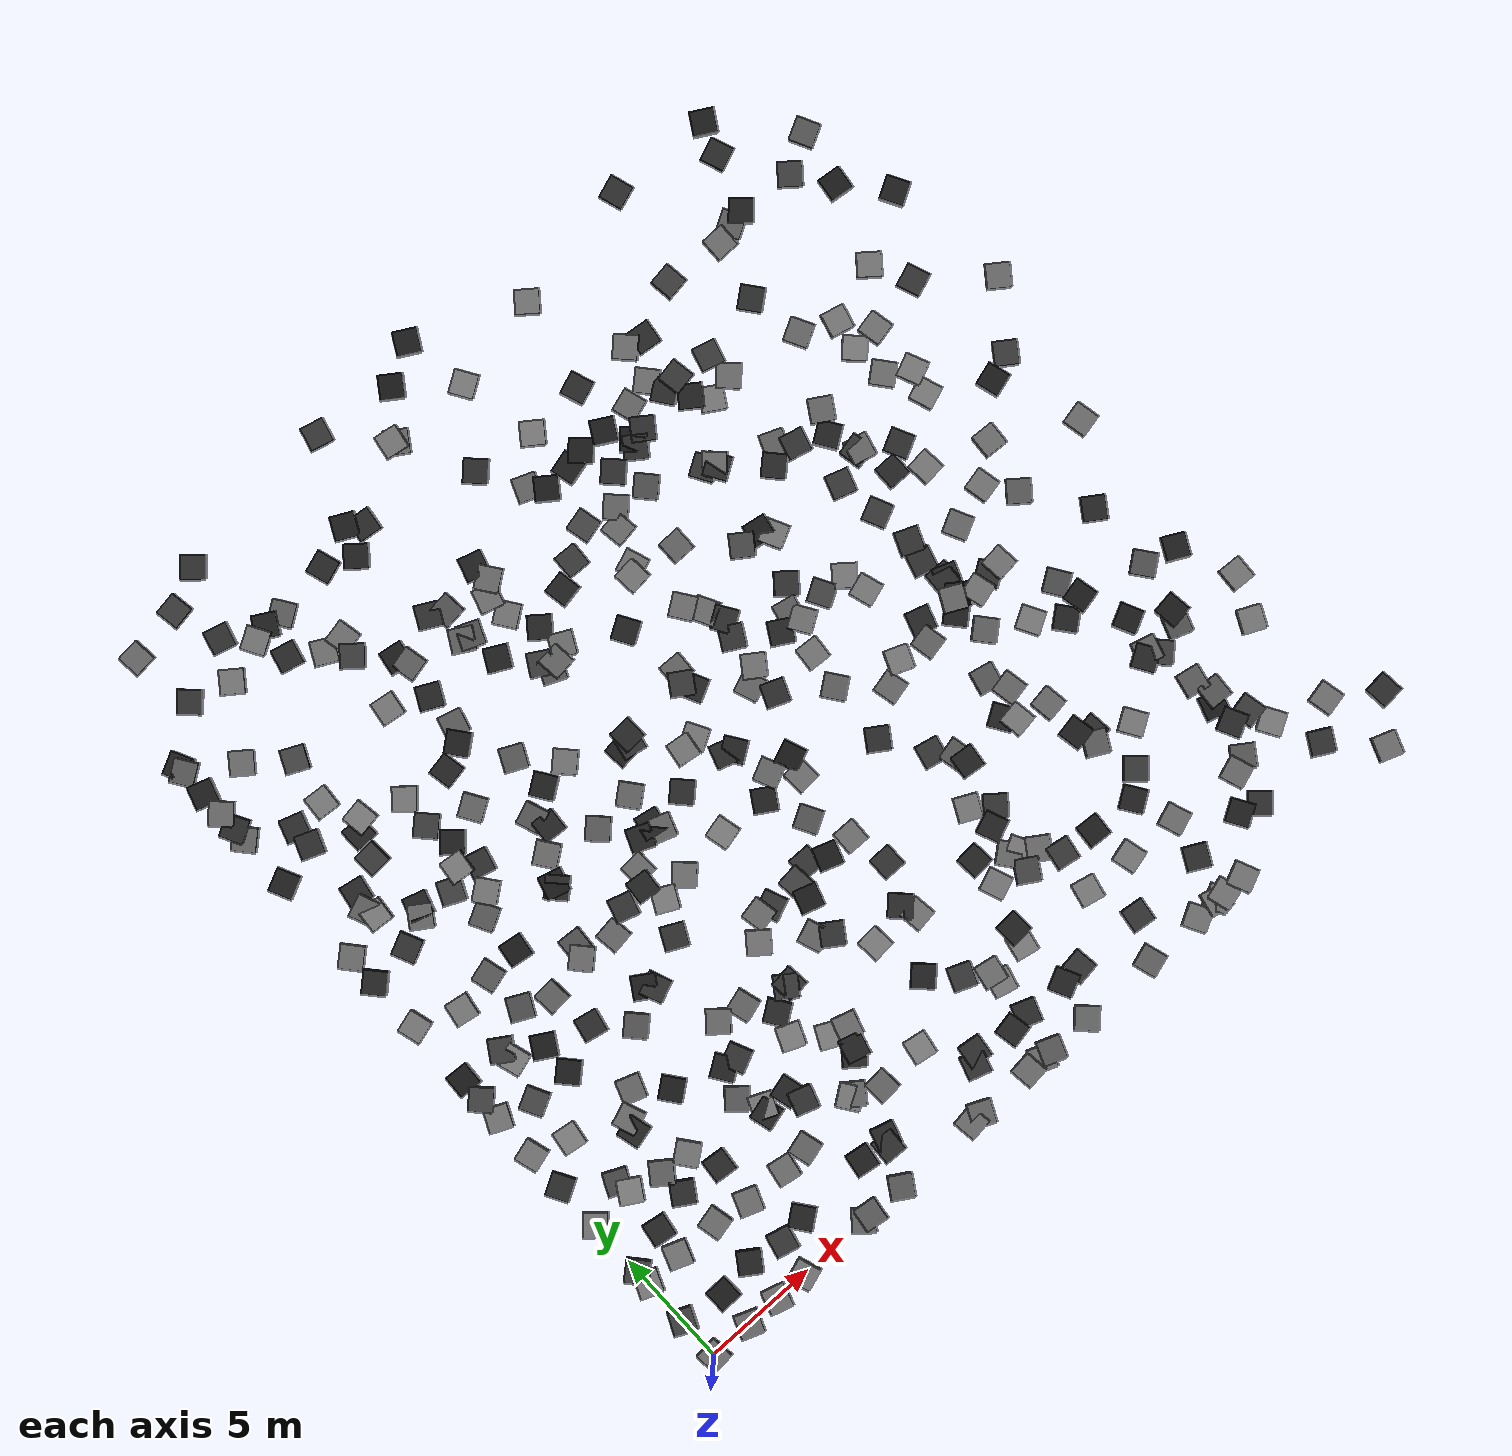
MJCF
<mujoco model="random_box_terrain">
    <compiler angle="degree" coordinate="local"/>
    <option timestep="0.01" gravity="0 0 -9.81" integrator="RK4"/>

    <worldbody>
        <body name="terrain">
<geom type="box" pos="0.0 0.0 0.1" size="0.5 0.5 0.1" euler="2.838292851201259 1.8161851281568149 274.70912718223985" rgba="0.4475740507615985 0.4475740507615985 0.4475740507615985 1"/>
<geom type="box" pos="0.0 1.8513459430592916 0.13279954035127103" size="0.5 0.5 0.1" euler="-1.4980232287640345 -2.9181760496031672 246.0393778196559" rgba="0.242818058170565 0.242818058170565 0.242818058170565 1"/>
<geom type="box" pos="0.0 3.8562291817168077 0.16061113573103714" size="0.5 0.5 0.1" euler="-2.0541181039971996 1.125839000708785 338.48071796022555" rgba="0.4786149483163924 0.4786149483163924 0.4786149483163924 1"/>
<geom type="box" pos="0.0 4.504896218908177 0.16752854276058854" size="0.5 0.5 0.1" euler="1.8660055316565929 -0.07669010120535225 130.7038243170307" rgba="0.25300595340029597 0.25300595340029597 0.25300595340029597 1"/>
<geom type="box" pos="0.0 6.967721179779196 0.15339745571612218" size="0.5 0.5 0.1" euler="0.9473556621498309 0.19779746663910736 48.48585498123146" rgba="0.47296555252499484 0.47296555252499484 0.47296555252499484 1"/>
<geom type="box" pos="0.0 8.999489546905888 0.20102876396078673" size="0.5 0.5 0.1" euler="0.06835291051515036 2.155411700712629 119.56119867658616" rgba="0.16972632905009616 0.16972632905009616 0.16972632905009616 1"/>
<geom type="box" pos="0.0 10.689925480385867 0.18780604094803288" size="0.5 0.5 0.1" euler="2.487404728873549 -0.3892828112090978 15.80864457848687" rgba="0.4743497086415107 0.4743497086415107 0.4743497086415107 1"/>
<geom type="box" pos="0.0 13.653662477376477 0.22947658603318213" size="0.5 0.5 0.1" euler="2.0927845456574694 -0.811903805198321 43.71335849451184" rgba="0.26642972966308887 0.26642972966308887 0.26642972966308887 1"/>
<geom type="box" pos="0.0 12.655006325756766 0.19900650661876879" size="0.5 0.5 0.1" euler="0.8278693663714698 -1.5685030881466815 335.5491674075012" rgba="0.4706160103102922 0.4706160103102922 0.4706160103102922 1"/>
<geom type="box" pos="0.0 14.674396924276703 0.2294252378138231" size="0.5 0.5 0.1" euler="2.0110574950219497 -0.46364839980836514 266.70718329003375" rgba="0.1038333312457198 0.1038333312457198 0.1038333312457198 1"/>
<geom type="box" pos="0.0 17.51274107126153 0.22981402792886968" size="0.5 0.5 0.1" euler="-0.9775702372529307 -0.47550689884962605 105.6123572259083" rgba="0.4733992589496594 0.4733992589496594 0.4733992589496594 1"/>
<geom type="box" pos="0.0 19.856484591805344 0.2755234804495783" size="0.5 0.5 0.1" euler="0.28868584192814595 -2.8848710343435453 41.53222296880692" rgba="0.14941188511779774 0.14941188511779774 0.14941188511779774 1"/>
<geom type="box" pos="0.0 21.209912039330803 0.29509987000398813" size="0.5 0.5 0.1" euler="-0.09185489736948416 -0.8162172570537125 40.96760343779037" rgba="0.42935434017758034 0.42935434017758034 0.42935434017758034 1"/>
<geom type="box" pos="0.0 25.115241446430026 0.3285222245624032" size="0.5 0.5 0.1" euler="2.490204295677403 1.944754420115883 25.16999877384545" rgba="0.12256862130148392 0.12256862130148392 0.12256862130148392 1"/>
<geom type="box" pos="0.0 27.470655963984868 0.2930102203538265" size="0.5 0.5 0.1" euler="0.17534809534255746 -2.111590469260043 311.3036285306654" rgba="0.40120252751399454 0.40120252751399454 0.40120252751399454 1"/>
<geom type="box" pos="0.0 28.03530950987368 0.32664839710455196" size="0.5 0.5 0.1" euler="-1.5574589595748474 -2.376050602734968 119.27884097866367" rgba="0.1641970052597792 0.1641970052597792 0.1641970052597792 1"/>
<geom type="box" pos="0.0 28.82628375202815 0.35406752110154593" size="0.5 0.5 0.1" euler="2.2508180361093153 0.7907231619304849 224.9975738755629" rgba="0.42496365971836103 0.42496365971836103 0.42496365971836103 1"/>
<geom type="box" pos="0.0 29.856190096788463 0.34492683724286693" size="0.5 0.5 0.1" euler="2.3016475698514345 -1.5839859557752696 251.78545080089586" rgba="0.12189925792121943 0.12189925792121943 0.12189925792121943 1"/>
<geom type="box" pos="0.0 31.011093619035353 0.3410801397545409" size="0.5 0.5 0.1" euler="-1.3211022215257924 -0.41629631678280443 124.02399609829048" rgba="0.34687241810474184 0.34687241810474184 0.34687241810474184 1"/>
<geom type="box" pos="0.0 31.312848182219216 0.3220329674901909" size="0.5 0.5 0.1" euler="-0.9828613341683199 1.4255625756910888 206.57697948150502" rgba="0.12444428817866432 0.12444428817866432 0.12444428817866432 1"/>
<geom type="box" pos="1.8511462246570616 0.0 0.1" size="0.5 0.5 0.1" euler="-0.08211464375147326 1.886115941642398 248.79151080836732" rgba="0.410714276457804 0.410714276457804 0.410714276457804 1"/>
<geom type="box" pos="1.903618456014361 1.5533132702361165 0.1" size="0.5 0.5 0.1" euler="2.3428282222242185 -0.4105998218192233 0.7092452477877664" rgba="0.11104045584274785 0.11104045584274785 0.11104045584274785 1"/>
<geom type="box" pos="1.6119800079505824 3.9202688076938683 0.1" size="0.5 0.5 0.1" euler="-0.8294022951449209 -2.227764215459171 249.9195293526132" rgba="0.46054694797776363 0.46054694797776363 0.46054694797776363 1"/>
<geom type="box" pos="1.7239606146479884 5.119674051954027 0.1" size="0.5 0.5 0.1" euler="0.2405658748148216 1.014558015711354 80.5031535408895" rgba="0.1461320090245582 0.1461320090245582 0.1461320090245582 1"/>
<geom type="box" pos="1.9139204472920162 7.042297549032044 0.14581890600986996" size="0.5 0.5 0.1" euler="-2.3905172805483534 0.12298337432795137 238.6696940435142" rgba="0.4977559611834361 0.4977559611834361 0.4977559611834361 1"/>
<geom type="box" pos="1.7652264614536939 7.639813124028922 0.10545167010806353" size="0.5 0.5 0.1" euler="2.594429398835085 1.0269427170294296 155.33792230350383" rgba="0.29365930506688165 0.29365930506688165 0.29365930506688165 1"/>
<geom type="box" pos="1.5394256402239668 10.17934052465327 0.1516941674527081" size="0.5 0.5 0.1" euler="-2.064645138613975 2.0563572381935966 351.61487701605165" rgba="0.49991960365733734 0.49991960365733734 0.49991960365733734 1"/>
<geom type="box" pos="1.5019078534645054 12.18055540072471 0.13205679541886267" size="0.5 0.5 0.1" euler="0.8777160990374484 -0.705311303355229 117.24966457870212" rgba="0.2804590717237246 0.2804590717237246 0.2804590717237246 1"/>
<geom type="box" pos="1.9890678159704147 13.94100446766184 0.1" size="0.5 0.5 0.1" euler="-0.3532766475613589 0.1918685964454836 106.95262618006514" rgba="0.49608063064642627 0.49608063064642627 0.49608063064642627 1"/>
<geom type="box" pos="1.8740268562299853 14.555863695539953 0.1" size="0.5 0.5 0.1" euler="-0.7908742769924366 1.560451679915193 147.21199358955084" rgba="0.2348948653976425 0.2348948653976425 0.2348948653976425 1"/>
<geom type="box" pos="1.7883748373388313 16.770430916243455 0.1" size="0.5 0.5 0.1" euler="1.7640653428006203 0.1502057714435283 350.18617822175037" rgba="0.48421261447631136 0.48421261447631136 0.48421261447631136 1"/>
<geom type="box" pos="1.8461650936195855 20.02349509626088 0.1" size="0.5 0.5 0.1" euler="-2.313926110976163 -1.1867758066282066 205.2074487628696" rgba="0.18346502834413606 0.18346502834413606 0.18346502834413606 1"/>
<geom type="box" pos="1.6136291738150013 22.239362908938485 0.11648345032943325" size="0.5 0.5 0.1" euler="2.8355656032022116 -1.5009954094037414 22.089623357076903" rgba="0.38892397640993526 0.38892397640993526 0.38892397640993526 1"/>
<geom type="box" pos="1.719836288816257 25.605168955220723 0.14365253334992856" size="0.5 0.5 0.1" euler="1.8527933654319177 -0.8612962705325842 68.27630752846018" rgba="0.180123408904705 0.180123408904705 0.180123408904705 1"/>
<geom type="box" pos="1.7974701137217661 21.823994540794963 0.13114959606911872" size="0.5 0.5 0.1" euler="-2.7338158847454075 0.32271000033231934 355.28142804010173" rgba="0.4880438537231192 0.4880438537231192 0.4880438537231192 1"/>
<geom type="box" pos="1.8096681469335547 22.96953386038673 0.10473573147823931" size="0.5 0.5 0.1" euler="1.4098964852414184 2.495727210753203 79.63386279168333" rgba="0.1579098798471062 0.1579098798471062 0.1579098798471062 1"/>
<geom type="box" pos="1.8945893853171216 29.798647533387975 0.1" size="0.5 0.5 0.1" euler="2.99340248126778 1.6533538067909728 142.59420802308563" rgba="0.4372907523046915 0.4372907523046915 0.4372907523046915 1"/>
<geom type="box" pos="1.7330924109544865 26.491199164677955 0.1" size="0.5 0.5 0.1" euler="1.7662392669423648 -0.2739555624718868 161.61200339837146" rgba="0.17719900076767683 0.17719900076767683 0.17719900076767683 1"/>
<geom type="box" pos="1.6073401574395998 35.61877035276025 0.12511141752619853" size="0.5 0.5 0.1" euler="1.9238325433706578 1.1421464033933875 4.8294628171911524" rgba="0.418002278898836 0.418002278898836 0.418002278898836 1"/>
<geom type="box" pos="1.992592007889125 32.95030771237645 0.1319865945540115" size="0.5 0.5 0.1" euler="1.5532560292109707 -1.6986794906333424 46.070622855848555" rgba="0.1960976234426116 0.1960976234426116 0.1960976234426116 1"/>
<geom type="box" pos="3.3390132515455804 0.0 0.12408445555746994" size="0.5 0.5 0.1" euler="-2.4194142448455964 2.4068025052602984 163.5529539497328" rgba="0.42713842810341307 0.42713842810341307 0.42713842810341307 1"/>
<geom type="box" pos="3.511106795442404 1.7976007025325673 0.13032899757207028" size="0.5 0.5 0.1" euler="1.069385036866814 0.6002952327986155 325.3427292875174" rgba="0.13745822676549657 0.13745822676549657 0.13745822676549657 1"/>
<geom type="box" pos="3.5515243429678782 3.8622987864494727 0.12987448561841858" size="0.5 0.5 0.1" euler="-2.0648935055383237 -1.0060914622371964 282.7207702640005" rgba="0.4219052975474157 0.4219052975474157 0.4219052975474157 1"/>
<geom type="box" pos="3.404924930633103 5.597260392576158 0.13686696800709255" size="0.5 0.5 0.1" euler="2.9096402771213805 1.1138254347364152 326.8775338802232" rgba="0.16750449248545735 0.16750449248545735 0.16750449248545735 1"/>
<geom type="box" pos="3.3180887012337723 6.739244382902319 0.16798543086729806" size="0.5 0.5 0.1" euler="-0.3323116507672177 -1.2946830263187055 54.23744132281905" rgba="0.37991661583689595 0.37991661583689595 0.37991661583689595 1"/>
<geom type="box" pos="3.6043437152999784 8.677413711429283 0.1" size="0.5 0.5 0.1" euler="2.664011350997649 0.4753366396017755 104.03156965547147" rgba="0.1500916895153838 0.1500916895153838 0.1500916895153838 1"/>
<geom type="box" pos="3.7876495777495105 9.180841611543112 0.12314861595766728" size="0.5 0.5 0.1" euler="2.97078565188672 1.715639198482065 199.82346649068285" rgba="0.44543923713183664 0.44543923713183664 0.44543923713183664 1"/>
<geom type="box" pos="3.271234192674669 12.147426772153995 0.15007460076633636" size="0.5 0.5 0.1" euler="-1.976930506677714 -1.1997588859292851 42.22972393892783" rgba="0.10595441444989238 0.10595441444989238 0.10595441444989238 1"/>
<geom type="box" pos="3.5587651804699383 15.293227279088326 0.12745543628525602" size="0.5 0.5 0.1" euler="0.8004674832932679 2.296540098284164 333.4744321902219" rgba="0.3089507114272559 0.3089507114272559 0.3089507114272559 1"/>
<geom type="box" pos="3.2224745587421246 13.538653745943842 0.1" size="0.5 0.5 0.1" euler="-2.9667616156442405 2.0448786946982844 59.36300489114342" rgba="0.10055027965569324 0.10055027965569324 0.10055027965569324 1"/>
<geom type="box" pos="3.4782369231085726 17.060646385560844 0.1476745713151853" size="0.5 0.5 0.1" euler="-1.397072616845141 1.1053013450707603 15.381479776682028" rgba="0.3517326723419065 0.3517326723419065 0.3517326723419065 1"/>
<geom type="box" pos="3.262298524398389 20.946600800302807 0.1" size="0.5 0.5 0.1" euler="-0.6724459825706592 -0.055094664716264674 162.16916397707158" rgba="0.13897536705401442 0.13897536705401442 0.13897536705401442 1"/>
<geom type="box" pos="3.0600096035046693 20.595622548938067 0.10594394965096302" size="0.5 0.5 0.1" euler="1.2297613912947405 -0.8449157929638469 146.158429209998" rgba="0.4165747069292114 0.4165747069292114 0.4165747069292114 1"/>
<geom type="box" pos="3.4709162548714234 24.62820031692796 0.13321054532703935" size="0.5 0.5 0.1" euler="2.8950841052476015 1.668908463964863 89.93132501007976" rgba="0.14842316978438982 0.14842316978438982 0.14842316978438982 1"/>
<geom type="box" pos="3.9157117242441997 25.060975001439708 0.16873202517547495" size="0.5 0.5 0.1" euler="-0.9139606786238783 2.007912772745966 8.877799859197077" rgba="0.49818507308278726 0.49818507308278726 0.49818507308278726 1"/>
<geom type="box" pos="3.1758538468503485 23.54051514881875 0.14652174662777961" size="0.5 0.5 0.1" euler="-2.2806423228047774 -1.0547516951342577 183.1855494062405" rgba="0.22385419321418767 0.22385419321418767 0.22385419321418767 1"/>
<geom type="box" pos="3.189247340996752 26.52342261728098 0.12068366460692012" size="0.5 0.5 0.1" euler="0.8451385261120947 2.7066748780650434 85.49212290205074" rgba="0.49157401039395465 0.49157401039395465 0.49157401039395465 1"/>
<geom type="box" pos="3.5466281276882405 28.491087154198468 0.14709962899871923" size="0.5 0.5 0.1" euler="1.2212521844398294 -1.5765308060420422 244.56180319582225" rgba="0.27783230582148066 0.27783230582148066 0.27783230582148066 1"/>
<geom type="box" pos="3.769944197057471 32.41805419901217 0.16567853955817283" size="0.5 0.5 0.1" euler="0.5824618386959717 0.8102780199551138 323.4496824988462" rgba="0.48081726705633854 0.48081726705633854 0.48081726705633854 1"/>
<geom type="box" pos="3.9599037541153534 35.99291076562212 0.13243729907864868" size="0.5 0.5 0.1" euler="-1.5950557352119485 0.8839940229480989 279.2501681936788" rgba="0.22860180141552378 0.22860180141552378 0.22860180141552378 1"/>
<geom type="box" pos="4.767172128524702 0.0 0.1" size="0.5 0.5 0.1" euler="2.821116926737389 -1.628090491139389 18.572499039651728" rgba="0.48044415939749474 0.48044415939749474 0.48044415939749474 1"/>
<geom type="box" pos="5.018089962049775 1.5175791578743243 0.1" size="0.5 0.5 0.1" euler="-1.0041732025890118 -2.1174088239872253 76.8265667385504" rgba="0.2085454511285522 0.2085454511285522 0.2085454511285522 1"/>
<geom type="box" pos="5.074939730687403 3.606073374102405 0.11958695168480502" size="0.5 0.5 0.1" euler="-0.9035668332095876 1.3545076739607778 159.2542805021619" rgba="0.42954830561149104 0.42954830561149104 0.42954830561149104 1"/>
<geom type="box" pos="5.19182835163618 5.4159823072778615 0.1" size="0.5 0.5 0.1" euler="1.841810215070681 -0.7980877274644413 174.132804095009" rgba="0.15748676364507244 0.15748676364507244 0.15748676364507244 1"/>
<geom type="box" pos="4.566719671766497 6.630062957035056 0.10884271153529884" size="0.5 0.5 0.1" euler="1.3251197931803151 0.2513823665699162 217.66600722263368" rgba="0.4679246443197612 0.4679246443197612 0.4679246443197612 1"/>
<geom type="box" pos="5.83178940747201 8.902619553697416 0.1" size="0.5 0.5 0.1" euler="2.226505692756641 -1.8438916036462032 37.279781034625394" rgba="0.1095296394761256 0.1095296394761256 0.1095296394761256 1"/>
<geom type="box" pos="4.633147159119467 9.990727368245675 0.1" size="0.5 0.5 0.1" euler="1.9709159230327424 0.6195362618732512 69.86320961985305" rgba="0.41064225989374503 0.41064225989374503 0.41064225989374503 1"/>
<geom type="box" pos="5.137163573542966 12.900652612757344 0.12207700853516668" size="0.5 0.5 0.1" euler="-1.9944701937715748 0.3087785700430441 78.43331754280956" rgba="0.1644389403624032 0.1644389403624032 0.1644389403624032 1"/>
<geom type="box" pos="4.775767642350756 14.767550399807863 0.1424140811102151" size="0.5 0.5 0.1" euler="-2.377793266384665 -2.420398040401627 4.127184088929559" rgba="0.3768173849446469 0.3768173849446469 0.3768173849446469 1"/>
<geom type="box" pos="4.944351294138636 17.07633647304036 0.1" size="0.5 0.5 0.1" euler="2.1581209814455455 -1.0570034942384028 171.38815539229873" rgba="0.10313858671973267 0.10313858671973267 0.10313858671973267 1"/>
<geom type="box" pos="4.931955760470554 18.891226562253195 0.14894675854259748" size="0.5 0.5 0.1" euler="-2.2565456857979704 2.1966382669050732 118.27416442660538" rgba="0.3402852279281964 0.3402852279281964 0.3402852279281964 1"/>
<geom type="box" pos="5.9472248949928455 21.9093377251567 0.1" size="0.5 0.5 0.1" euler="1.8671900325302282 0.6491365854936761 317.99224014501175" rgba="0.12239814822526225 0.12239814822526225 0.12239814822526225 1"/>
<geom type="box" pos="5.628681260525222 19.5891541976653 0.1" size="0.5 0.5 0.1" euler="-1.8383529612862446 2.6134926448231095 127.69837244215388" rgba="0.46534581270532993 0.46534581270532993 0.46534581270532993 1"/>
<geom type="box" pos="4.63318187934157 20.505768656434498 0.1452926961372959" size="0.5 0.5 0.1" euler="1.725519484191457 -0.9234486435727716 155.38474116808672" rgba="0.2599767574536185 0.2599767574536185 0.2599767574536185 1"/>
<geom type="box" pos="5.421079805932594 21.057993132071957 0.17527702728820727" size="0.5 0.5 0.1" euler="-1.8555450578050112 -1.965985556787041 353.617563684374" rgba="0.4927978154386571 0.4927978154386571 0.4927978154386571 1"/>
<geom type="box" pos="5.619300257656542 23.082020989494314 0.1" size="0.5 0.5 0.1" euler="-2.3647393933574867 1.9172098650605056 222.9752351715744" rgba="0.23304311071020237 0.23304311071020237 0.23304311071020237 1"/>
<geom type="box" pos="5.687733721292749 24.45385025486339 0.1" size="0.5 0.5 0.1" euler="-0.616444580644981 -0.6979903223806452 138.5693694083358" rgba="0.4762351870352487 0.4762351870352487 0.4762351870352487 1"/>
<geom type="box" pos="4.548283089311347 33.99799098545487 0.1" size="0.5 0.5 0.1" euler="2.7581405733486237 -1.4024420566441014 344.27721608405494" rgba="0.19153222319091717 0.19153222319091717 0.19153222319091717 1"/>
<geom type="box" pos="5.551081960702787 32.98410263462075 0.14908244867899764" size="0.5 0.5 0.1" euler="0.07324690222438424 -0.8839242230090907 300.3493831840629" rgba="0.471762063658158 0.471762063658158 0.471762063658158 1"/>
<geom type="box" pos="5.665866560460092 36.780118322801755 0.15688544627734952" size="0.5 0.5 0.1" euler="-1.0988573931286165 1.67694347199848 228.68146980557822" rgba="0.18038317210203503 0.18038317210203503 0.18038317210203503 1"/>
<geom type="box" pos="7.9470883528668725 0.0 0.13679345993058" size="0.5 0.5 0.1" euler="-2.217580043847621 0.8767408280441877 230.6268715505228" rgba="0.3885257430395528 0.3885257430395528 0.3885257430395528 1"/>
<geom type="box" pos="6.228447738877564 1.7126804702858738 0.10888045962144871" size="0.5 0.5 0.1" euler="0.691971201345468 -1.6592249264687875 217.13616376788153" rgba="0.1334691366706695 0.1334691366706695 0.1334691366706695 1"/>
<geom type="box" pos="6.963648755286259 3.5652846300683043 0.1" size="0.5 0.5 0.1" euler="-2.69797358019263 -0.8564200297345139 80.26092297010896" rgba="0.4268435765497457 0.4268435765497457 0.4268435765497457 1"/>
<geom type="box" pos="7.948566929008271 5.679066891212382 0.10957508109134594" size="0.5 0.5 0.1" euler="-0.2754970611794034 2.5404088725734137 194.74182285896143" rgba="0.13803484570429633 0.13803484570429633 0.13803484570429633 1"/>
<geom type="box" pos="7.45903006490911 6.906389104119389 0.1" size="0.5 0.5 0.1" euler="1.3580800745940138 2.2247329084745457 138.66780971622964" rgba="0.35138759271671305 0.35138759271671305 0.35138759271671305 1"/>
<geom type="box" pos="7.914515833365142 8.138595125476174 0.1" size="0.5 0.5 0.1" euler="0.877807171597726 1.5048445222053655 123.60160044569315" rgba="0.13432703597596027 0.13432703597596027 0.13432703597596027 1"/>
<geom type="box" pos="6.461245034794567 11.706940707572764 0.14959833715730197" size="0.5 0.5 0.1" euler="1.7911521985440864 0.46966067189385186 132.65018693390746" rgba="0.3369080855983201 0.3369080855983201 0.3369080855983201 1"/>
<geom type="box" pos="7.7170330180856785 12.621790959870419 0.1053702047657332" size="0.5 0.5 0.1" euler="1.6625634369677105 -0.2844861352979975 147.21465738196622" rgba="0.11606080160827968 0.11606080160827968 0.11606080160827968 1"/>
<geom type="box" pos="6.838872784330905 15.66814409341891 0.1" size="0.5 0.5 0.1" euler="2.7479729745439325 -0.89628610289913 86.04492345599749" rgba="0.3297391885917135 0.3297391885917135 0.3297391885917135 1"/>
<geom type="box" pos="7.813272234202685 17.998200043486726 0.11075342398219828" size="0.5 0.5 0.1" euler="-0.4094209047674826 2.072015485997171 164.24664503116082" rgba="0.10117433782801184 0.10117433782801184 0.10117433782801184 1"/>
<geom type="box" pos="6.656145620852644 15.120778673207134 0.1550496253200368" size="0.5 0.5 0.1" euler="0.12845250412782683 -2.1074738863888474 222.11588858525167" rgba="0.42562993838776675 0.42562993838776675 0.42562993838776675 1"/>
<geom type="box" pos="7.801071087406798 17.834160755939276 0.1" size="0.5 0.5 0.1" euler="2.602178570767439 -0.8583729820721371 312.67458153697356" rgba="0.15639894468040547 0.15639894468040547 0.15639894468040547 1"/>
<geom type="box" pos="7.456425333931451 22.39434575869733 0.1" size="0.5 0.5 0.1" euler="2.72299839904046 -2.6444935418811184 301.8748301924212" rgba="0.4078909933951389 0.4078909933951389 0.4078909933951389 1"/>
<geom type="box" pos="6.177083102270406 20.570379564144048 0.1" size="0.5 0.5 0.1" euler="2.4363477701125857 -1.6587168670165153 345.1581753579515" rgba="0.18997849424846236 0.18997849424846236 0.18997849424846236 1"/>
<geom type="box" pos="7.603273371761097 27.516257926603565 0.1430741174646729" size="0.5 0.5 0.1" euler="1.8955002314891756 -0.5643148316379216 171.2328199471601" rgba="0.4840517217057405 0.4840517217057405 0.4840517217057405 1"/>
<geom type="box" pos="7.95007388778332 29.992173086881397 0.11121423660011907" size="0.5 0.5 0.1" euler="2.205165027403832 0.03915794422445007 229.89421513919046" rgba="0.24365732245236502 0.24365732245236502 0.24365732245236502 1"/>
<geom type="box" pos="7.25076314412474 30.857703935992216 0.10396041032914134" size="0.5 0.5 0.1" euler="1.0742933017497762 2.2238515459557435 332.5384965063715" rgba="0.4476772136335959 0.4476772136335959 0.4476772136335959 1"/>
<geom type="box" pos="6.046334448363295 31.67616510479687 0.1496006963226537" size="0.5 0.5 0.1" euler="2.9232159551846015 2.0212024687717713 76.02172537012059" rgba="0.1590836912166247 0.1590836912166247 0.1590836912166247 1"/>
<geom type="box" pos="7.028968328762255 33.08722500728293 0.10599516680645693" size="0.5 0.5 0.1" euler="-1.7847329213810046 2.7076996098764745 124.41446202190552" rgba="0.3643548360856729 0.3643548360856729 0.3643548360856729 1"/>
<geom type="box" pos="6.223853070460607 33.15298505893005 0.13553424744131717" size="0.5 0.5 0.1" euler="0.17767638850570666 -0.9429859605152151 150.2023079777004" rgba="0.12286916977172879 0.12286916977172879 0.12286916977172879 1"/>
<geom type="box" pos="8.302282439958233 0.0 0.1680900328162499" size="0.5 0.5 0.1" euler="-1.9578058371339597 -2.0052758328791205 82.38011825140138" rgba="0.3567836319872397 0.3567836319872397 0.3567836319872397 1"/>
<geom type="box" pos="9.493375153819684 1.7842534972945354 0.1" size="0.5 0.5 0.1" euler="-0.10177948641939727 0.8176278251973588 171.14329646159572" rgba="0.12119151717340344 0.12119151717340344 0.12119151717340344 1"/>
<geom type="box" pos="8.14916688110777 3.6531925318510003 0.1" size="0.5 0.5 0.1" euler="-0.7356295936569222 1.3900997359270306 105.16168936443853" rgba="0.38834521041049885 0.38834521041049885 0.38834521041049885 1"/>
<geom type="box" pos="9.121949114218939 5.773111525673553 0.1" size="0.5 0.5 0.1" euler="-1.378384140862201 2.9211836061635825 194.42295483026908" rgba="0.1369625339182465 0.1369625339182465 0.1369625339182465 1"/>
<geom type="box" pos="8.025370369371052 6.002423653145834 0.1" size="0.5 0.5 0.1" euler="-1.969871453102982 1.4403312538984627 335.8607523676736" rgba="0.4675962445550884 0.4675962445550884 0.4675962445550884 1"/>
<geom type="box" pos="8.542514752574172 8.096994442888588 0.1181627941378954" size="0.5 0.5 0.1" euler="-1.8264167908008564 -2.933783633641557 114.75698300315982" rgba="0.19768472086509903 0.19768472086509903 0.19768472086509903 1"/>
<geom type="box" pos="8.962513108854434 9.66124081487718 0.1" size="0.5 0.5 0.1" euler="-2.1265011833705634 -1.1193268586506149 319.5304067560018" rgba="0.40986939093920893 0.40986939093920893 0.40986939093920893 1"/>
<geom type="box" pos="8.045082638773998 12.303149017228495 0.1" size="0.5 0.5 0.1" euler="-0.6787713368992936 2.5612861693015656 201.70306016638122" rgba="0.1928065594948748 0.1928065594948748 0.1928065594948748 1"/>
<geom type="box" pos="8.194506110819402 14.936665000123574 0.12702146012145527" size="0.5 0.5 0.1" euler="2.6976446636732723 1.8786851715753983 187.35038769604253" rgba="0.41779845549021555 0.41779845549021555 0.41779845549021555 1"/>
<geom type="box" pos="9.223705288521058 15.483969433714254 0.14999434763015665" size="0.5 0.5 0.1" euler="1.8296114034480144 0.4105949681951664 72.53789152752611" rgba="0.20210352632031478 0.20210352632031478 0.20210352632031478 1"/>
<geom type="box" pos="8.38523563530552 19.068912932567894 0.13647919678902393" size="0.5 0.5 0.1" euler="1.7210211318267277 -2.964034729336729 306.01807418885573" rgba="0.4317355386760171 0.4317355386760171 0.4317355386760171 1"/>
<geom type="box" pos="9.192804198553988 19.831399351346793 0.1" size="0.5 0.5 0.1" euler="1.270281281957872 2.3547454585689565 85.75700815885429" rgba="0.14725050388950123 0.14725050388950123 0.14725050388950123 1"/>
<geom type="box" pos="8.940913840171707 20.518995754579144 0.10770783698720597" size="0.5 0.5 0.1" euler="1.759551981157066 -2.3391692046071584 110.18967808421614" rgba="0.355575151097829 0.355575151097829 0.355575151097829 1"/>
<geom type="box" pos="7.677044569370692 24.146501866171654 0.1" size="0.5 0.5 0.1" euler="-2.5886656189012647 1.9602753797093104 100.80818659531634" rgba="0.13468937986485718 0.13468937986485718 0.13468937986485718 1"/>
<geom type="box" pos="9.104747607647322 25.320641397214043 0.1" size="0.5 0.5 0.1" euler="2.5568957036732467 2.1174664971155277 254.73415434888395" rgba="0.3729229124075316 0.3729229124075316 0.3729229124075316 1"/>
<geom type="box" pos="8.72465919460029 24.652501746942875 0.12893648098194266" size="0.5 0.5 0.1" euler="0.665375947030693 -0.6086450531035554 308.11746258323416" rgba="0.11700412297176843 0.11700412297176843 0.11700412297176843 1"/>
<geom type="box" pos="9.414061137262761 28.247212674022315 0.12120632424450306" size="0.5 0.5 0.1" euler="-0.7727567011732539 -0.544975494856101 12.490170855840006" rgba="0.37462140107673303 0.37462140107673303 0.37462140107673303 1"/>
<geom type="box" pos="9.140168736498008 26.754125685321064 0.15777156662549285" size="0.5 0.5 0.1" euler="-2.3756018542645245 2.4387570917029304 63.166893076565565" rgba="0.1368376114473423 0.1368376114473423 0.1368376114473423 1"/>
<geom type="box" pos="8.175157578587696 30.77984908133313 0.11627989845207057" size="0.5 0.5 0.1" euler="2.5328796688642994 2.5627962591638864 11.7856170836072" rgba="0.4521681274450665 0.4521681274450665 0.4521681274450665 1"/>
<geom type="box" pos="9.454020889019349 33.35602083181109 0.1" size="0.5 0.5 0.1" euler="-0.6163776057384096 -1.0607800815036994 287.77359572443186" rgba="0.14739704925098684 0.14739704925098684 0.14739704925098684 1"/>
<geom type="box" pos="9.937611607951219 0.0 0.1559258289419635" size="0.5 0.5 0.1" euler="2.906610405087088 0.8227703227903422 57.8975125000958" rgba="0.36089662062594285 0.36089662062594285 0.36089662062594285 1"/>
<geom type="box" pos="10.81386145784997 1.8519091159890104 0.12700345260299756" size="0.5 0.5 0.1" euler="-0.7750905690737477 0.8971420896237978 73.11461944472708" rgba="0.1490003922392488 0.1490003922392488 0.1490003922392488 1"/>
<geom type="box" pos="10.984149962804075 3.95700138484378 0.1" size="0.5 0.5 0.1" euler="-2.58727433316771 -0.4340840198285729 53.63304773718573" rgba="0.40039442688821925 0.40039442688821925 0.40039442688821925 1"/>
<geom type="box" pos="9.370489227296556 5.108131215050989 0.1402700106612936" size="0.5 0.5 0.1" euler="2.169436356922419 -2.701792673999412 161.8326336194355" rgba="0.1952045580596575 0.1952045580596575 0.1952045580596575 1"/>
<geom type="box" pos="11.838297792661187 6.309434801242582 0.1" size="0.5 0.5 0.1" euler="-2.598089484748438 2.1287838425634664 153.58583729161558" rgba="0.492425495352496 0.492425495352496 0.492425495352496 1"/>
<geom type="box" pos="10.925494110719473 8.344854201960878 0.1" size="0.5 0.5 0.1" euler="1.6710147843344947 -0.9132543853317348 214.68857018002026" rgba="0.1557563563505432 0.1557563563505432 0.1557563563505432 1"/>
<geom type="box" pos="10.120332471069897 9.455696358961918 0.12413809514090979" size="0.5 0.5 0.1" euler="-2.0673471689983494 -2.8960096249385954 16.38812855296716" rgba="0.39057763708779714 0.39057763708779714 0.39057763708779714 1"/>
<geom type="box" pos="9.927134563888472 13.282301768402737 0.11882457071777679" size="0.5 0.5 0.1" euler="-1.1801253535923302 1.6069177668771175 243.47862596364334" rgba="0.18597186221869091 0.18597186221869091 0.18597186221869091 1"/>
<geom type="box" pos="10.647940268206899 14.62520971716367 0.12460979578259768" size="0.5 0.5 0.1" euler="-2.2064086561445553 -2.0670428922217727 63.03192143310072" rgba="0.49581086095830895 0.49581086095830895 0.49581086095830895 1"/>
<geom type="box" pos="10.330600489899325 15.563782956087728 0.13090629732932496" size="0.5 0.5 0.1" euler="2.872612520893651 -0.8814641714313676 85.147075016291" rgba="0.1451947475952704 0.1451947475952704 0.1451947475952704 1"/>
<geom type="box" pos="10.552423791162221 18.456587937667134 0.14148852185710142" size="0.5 0.5 0.1" euler="-0.017475385328222792 -0.670470299159629 134.91672735714604" rgba="0.3537465547328855 0.3537465547328855 0.3537465547328855 1"/>
<geom type="box" pos="11.55235261931914 17.052023774389255 0.1396270960207755" size="0.5 0.5 0.1" euler="1.5907228577647778 -2.8362648933156107 67.41599797820248" rgba="0.141854819056929 0.141854819056929 0.141854819056929 1"/>
<geom type="box" pos="9.95864246904077 22.751695344118843 0.1" size="0.5 0.5 0.1" euler="2.7238483533846916 -0.39175901839672633 334.06919932392475" rgba="0.3617808213219317 0.3617808213219317 0.3617808213219317 1"/>
<geom type="box" pos="10.102312169125465 21.13330880127282 0.1" size="0.5 0.5 0.1" euler="-2.0863097332865035 -2.1278282587132047 34.587362799986224" rgba="0.11981802300178993 0.11981802300178993 0.11981802300178993 1"/>
<geom type="box" pos="11.948084871735947 27.475601782497442 0.1" size="0.5 0.5 0.1" euler="0.6554340356270973 1.8229934987168637 157.06726807771034" rgba="0.32071857556274286 0.32071857556274286 0.32071857556274286 1"/>
<geom type="box" pos="9.17658502564237 28.767782955979637 0.10048409356636634" size="0.5 0.5 0.1" euler="-0.8909265461084939 1.6671354918635668 81.1290541456797" rgba="0.10745355394206052 0.10745355394206052 0.10745355394206052 1"/>
<geom type="box" pos="11.907796831696846 28.825487252985248 0.1" size="0.5 0.5 0.1" euler="2.273676604634063 -1.7035425770124273 275.3163368847133" rgba="0.3332813614508692 0.3332813614508692 0.3332813614508692 1"/>
<geom type="box" pos="11.154668569469997 33.97008020502824 0.13107492189438744" size="0.5 0.5 0.1" euler="2.1232520952806544 -1.641847242048854 63.02493972522285" rgba="0.11950500994117715 0.11950500994117715 0.11950500994117715 1"/>
<geom type="box" pos="11.584270787877262 27.560604472886745 0.1" size="0.5 0.5 0.1" euler="2.659516062455997 -2.2286714081388377 240.12026973523515" rgba="0.38730711793353845 0.38730711793353845 0.38730711793353845 1"/>
<geom type="box" pos="10.69474849272654 32.79984188078641 0.1" size="0.5 0.5 0.1" euler="1.0327141952726144 1.4545911037437476 320.83887824601317" rgba="0.12847309085772982 0.12847309085772982 0.12847309085772982 1"/>
<geom type="box" pos="13.676660047138412 0.0 0.12602714791375408" size="0.5 0.5 0.1" euler="-1.3645640269028292 2.3293913746531922 277.6703863718242" rgba="0.4278951694633971 0.4278951694633971 0.4278951694633971 1"/>
<geom type="box" pos="10.625586388691225 1.5093348701450184 0.14692722443286355" size="0.5 0.5 0.1" euler="-2.439213783250191 -0.6654807718857967 87.84035214925579" rgba="0.18022622257681697 0.18022622257681697 0.18022622257681697 1"/>
<geom type="box" pos="10.803847676142901 3.9705177664081113 0.11106031323887618" size="0.5 0.5 0.1" euler="2.249496700489222 2.344360256773326 214.8682217152191" rgba="0.4897727524045331 0.4897727524045331 0.4897727524045331 1"/>
<geom type="box" pos="12.247081314327133 5.296391143571171 0.13529544334609445" size="0.5 0.5 0.1" euler="-0.362810750408626 0.6743978681253866 344.74430671272813" rgba="0.135280488677189 0.135280488677189 0.135280488677189 1"/>
<geom type="box" pos="10.674294522775888 7.297168355665405 0.104428085598725" size="0.5 0.5 0.1" euler="-2.6297718719959975 0.2398821462957006 337.44761300742385" rgba="0.4983308258881457 0.4983308258881457 0.4983308258881457 1"/>
<geom type="box" pos="11.863508837155726 8.88040571904735 0.13056618154224464" size="0.5 0.5 0.1" euler="0.696921769327437 -0.8692358788321197 235.4367700057708" rgba="0.21814604262107895 0.21814604262107895 0.21814604262107895 1"/>
<geom type="box" pos="12.992278695100978 11.701115151552042 0.12672251156472955" size="0.5 0.5 0.1" euler="2.498912436197539 -0.680540030549758 100.98041413618509" rgba="0.43929561816198026 0.43929561816198026 0.43929561816198026 1"/>
<geom type="box" pos="13.587789606868306 11.621587530237345 0.1" size="0.5 0.5 0.1" euler="-1.0942726033457661 -1.6334165153660727 111.65869260419312" rgba="0.20724641285282322 0.20724641285282322 0.20724641285282322 1"/>
<geom type="box" pos="11.85525503070948 14.832350273260998 0.13882725870745266" size="0.5 0.5 0.1" euler="1.2093137407617496 -1.6699488325302188 225.8606676399048" rgba="0.4504136032992385 0.4504136032992385 0.4504136032992385 1"/>
<geom type="box" pos="12.2321887285465 17.19899090448363 0.14407280878866335" size="0.5 0.5 0.1" euler="-1.9193408841063329 2.3170608618992645 79.07316603288804" rgba="0.12396118450379984 0.12396118450379984 0.12396118450379984 1"/>
<geom type="box" pos="10.672531690115367 16.212013578653718 0.127099540392097" size="0.5 0.5 0.1" euler="1.3126469062810129 1.0112541323771627 2.4251989821547726" rgba="0.4312592084814212 0.4312592084814212 0.4312592084814212 1"/>
<geom type="box" pos="13.751009516745434 20.116478001973476 0.14264355865054934" size="0.5 0.5 0.1" euler="1.529948615103999 1.2889577724762926 349.3172595148799" rgba="0.20101626367752395 0.20101626367752395 0.20101626367752395 1"/>
<geom type="box" pos="11.35885853523368 21.28831166828577 0.1" size="0.5 0.5 0.1" euler="-2.0848919581248007 1.9624700885089492 133.1837516525979" rgba="0.45479174322705773 0.45479174322705773 0.45479174322705773 1"/>
<geom type="box" pos="13.238351790296493 24.78651922439907 0.12294023488412638" size="0.5 0.5 0.1" euler="0.21392320249157581 -2.554483819751017 149.53571511385599" rgba="0.24424857146166798 0.24424857146166798 0.24424857146166798 1"/>
<geom type="box" pos="13.573917612876157 27.122163101966958 0.1" size="0.5 0.5 0.1" euler="-2.154685718613556 -1.7523643331171384 35.32788255728595" rgba="0.4575973602974962 0.4575973602974962 0.4575973602974962 1"/>
<geom type="box" pos="12.127879591482635 26.072231182560024 0.12977978192760664" size="0.5 0.5 0.1" euler="-0.03786253480151913 -2.582334844262988 241.8343062891806" rgba="0.12824666857344158 0.12824666857344158 0.12824666857344158 1"/>
<geom type="box" pos="13.447139457163546 28.093911528763158 0.1" size="0.5 0.5 0.1" euler="-1.8414794621121926 -0.6820290701943006 73.02885213269565" rgba="0.4414947609233405 0.4414947609233405 0.4414947609233405 1"/>
<geom type="box" pos="11.245943349084776 29.15378064147644 0.1" size="0.5 0.5 0.1" euler="0.616636803781784 -0.6534461592754486 331.7449561856616" rgba="0.18463999435738235 0.18463999435738235 0.18463999435738235 1"/>
<geom type="box" pos="13.955768766428829 28.648583494789182 0.11741194588151244" size="0.5 0.5 0.1" euler="-1.111426767495994 0.875413994402602 36.21656625697084" rgba="0.4151929326466798 0.4151929326466798 0.4151929326466798 1"/>
<geom type="box" pos="11.777397725895366 33.49690561712977 0.13176256392965577" size="0.5 0.5 0.1" euler="-0.8659207675703549 -2.5453528979954507 262.3930071709705" rgba="0.15817465651942522 0.15817465651942522 0.15817465651942522 1"/>
<geom type="box" pos="14.198473144900074 0.0 0.1" size="0.5 0.5 0.1" euler="2.944936874097696 2.641301122269134 64.55348868213767" rgba="0.40198598848521194 0.40198598848521194 0.40198598848521194 1"/>
<geom type="box" pos="15.324516724779986 1.5860068463322143 0.1" size="0.5 0.5 0.1" euler="0.20605092370160794 -1.526393423188128 162.66971885505302" rgba="0.19599285231058464 0.19599285231058464 0.19599285231058464 1"/>
<geom type="box" pos="12.05017814510828 3.4395094088143816 0.12791551945560642" size="0.5 0.5 0.1" euler="-0.6267756011107615 -0.07441756544637812 183.67359424113286" rgba="0.3982424945442118 0.3982424945442118 0.3982424945442118 1"/>
<geom type="box" pos="12.042130036358147 5.087499943494941 0.10882569644410053" size="0.5 0.5 0.1" euler="2.348319243255661 0.8241250240501818 51.729366676906594" rgba="0.15285257988330503 0.15285257988330503 0.15285257988330503 1"/>
<geom type="box" pos="12.599767642898907 6.100258560910984 0.12122733022187819" size="0.5 0.5 0.1" euler="-0.6722713957371642 -1.2745925574356627 253.12957264200813" rgba="0.4262100076728933 0.4262100076728933 0.4262100076728933 1"/>
<geom type="box" pos="12.04265597225129 8.861550212633416 0.12276170839829553" size="0.5 0.5 0.1" euler="2.127163034234421 1.2560350625530186 186.10774583904524" rgba="0.19435474283990725 0.19435474283990725 0.19435474283990725 1"/>
<geom type="box" pos="12.23176978000017 10.897580375764914 0.16237451014642412" size="0.5 0.5 0.1" euler="2.8625174061515004 -2.4687940605352123 51.97177719053671" rgba="0.47089718276820547 0.47089718276820547 0.47089718276820547 1"/>
<geom type="box" pos="14.905214725317945 11.642050062181461 0.1336737978647625" size="0.5 0.5 0.1" euler="1.1027407657328077 -2.6347050997653145 5.96380200285874" rgba="0.26896090817891294 0.26896090817891294 0.26896090817891294 1"/>
<geom type="box" pos="14.093877102060809 15.042355999714983 0.11315202430840825" size="0.5 0.5 0.1" euler="-2.2040558275140603 -0.24077073435139562 13.290691266710489" rgba="0.4975100256484454 0.4975100256484454 0.4975100256484454 1"/>
<geom type="box" pos="13.976797125462564 17.306253237136414 0.10927008265493132" size="0.5 0.5 0.1" euler="0.951270480220586 1.6133060898521467 223.08649329226253" rgba="0.1665451834144242 0.1665451834144242 0.1665451834144242 1"/>
<geom type="box" pos="12.421071520884821 16.79866408644966 0.1470345654164643" size="0.5 0.5 0.1" euler="1.9184411116452926 -1.6893661777093616 340.4310590254545" rgba="0.4052078502249232 0.4052078502249232 0.4052078502249232 1"/>
<geom type="box" pos="13.89299133485553 20.40085929804204 0.18195578376307528" size="0.5 0.5 0.1" euler="0.7126962032748807 -1.2839506911854117 181.3801591439733" rgba="0.15578604722588274 0.15578604722588274 0.15578604722588274 1"/>
<geom type="box" pos="12.36637759908546 18.595295997238967 0.1" size="0.5 0.5 0.1" euler="1.3291712427371438 -2.6270421593704545 38.765322564923174" rgba="0.4021740259256489 0.4021740259256489 0.4021740259256489 1"/>
<geom type="box" pos="13.332606029952984 20.096308676310308 0.1" size="0.5 0.5 0.1" euler="2.725633191235292 -2.4441398832767445 5.182267182564968" rgba="0.12828604064241864 0.12828604064241864 0.12828604064241864 1"/>
<geom type="box" pos="14.374772022153351 24.76581782735546 0.1" size="0.5 0.5 0.1" euler="-2.3818904271137162 1.5135501264143567 153.36686179996636" rgba="0.42903387624024336 0.42903387624024336 0.42903387624024336 1"/>
<geom type="box" pos="15.846877043431924 26.36780082677408 0.1" size="0.5 0.5 0.1" euler="-2.219006212342652 0.7890654810467774 280.02314679038886" rgba="0.1309990648173417 0.1309990648173417 0.1309990648173417 1"/>
<geom type="box" pos="13.419758147896186 24.299434338849295 0.1" size="0.5 0.5 0.1" euler="2.113363737535491 -0.1637571102951343 246.37766159876617" rgba="0.3433690310274139 0.3433690310274139 0.3433690310274139 1"/>
<geom type="box" pos="13.876680486734486 29.391616389024396 0.10964839879620031" size="0.5 0.5 0.1" euler="0.17936402849979682 2.9613774757565023 343.9877734190809" rgba="0.12634234625035876 0.12634234625035876 0.12634234625035876 1"/>
<geom type="box" pos="14.90074134218063 35.057727047881194 0.1" size="0.5 0.5 0.1" euler="1.4747617891113567 0.7861468059439787 236.44253460997626" rgba="0.4133038358685267 0.4133038358685267 0.4133038358685267 1"/>
<geom type="box" pos="12.773435952534642 37.378499377659004 0.1" size="0.5 0.5 0.1" euler="-0.540765294361552 2.9470040476351347 345.6677523924286" rgba="0.20956127039212574 0.20956127039212574 0.20956127039212574 1"/>
<geom type="box" pos="17.442699104769787 0.0 0.1" size="0.5 0.5 0.1" euler="0.039852632707076285 -2.690606344943986 69.20244574489551" rgba="0.42009199529267005 0.42009199529267005 0.42009199529267005 1"/>
<geom type="box" pos="15.656205250461277 1.9867691324086107 0.12037872863304397" size="0.5 0.5 0.1" euler="2.6078411617287056 -0.5332508818241966 82.9785298823329" rgba="0.18855540429395365 0.18855540429395365 0.18855540429395365 1"/>
<geom type="box" pos="14.148625624584891 3.554442533890782 0.1" size="0.5 0.5 0.1" euler="-2.665885978314857 0.8379922707829652 170.31109515383903" rgba="0.49837362243619043 0.49837362243619043 0.49837362243619043 1"/>
<geom type="box" pos="16.140500832126943 5.555509244909595 0.14320157672367706" size="0.5 0.5 0.1" euler="1.3743496290127775 2.0083822200845542 45.43889556802953" rgba="0.13233300371678533 0.13233300371678533 0.13233300371678533 1"/>
<geom type="box" pos="15.61472722093384 7.767317351639804 0.1" size="0.5 0.5 0.1" euler="-2.8368514380030287 -0.606964561507711 274.2693459873337" rgba="0.4935329490058592 0.4935329490058592 0.4935329490058592 1"/>
<geom type="box" pos="14.594130772180707 9.180638628571442 0.1" size="0.5 0.5 0.1" euler="-2.3678458030832306 2.6206097022646944 55.71337828199213" rgba="0.18964920825247164 0.18964920825247164 0.18964920825247164 1"/>
<geom type="box" pos="14.014882293500913 9.616086781345963 0.1" size="0.5 0.5 0.1" euler="-1.4320205127221337 1.6555928102841069 20.61112306046887" rgba="0.3922879605558879 0.3922879605558879 0.3922879605558879 1"/>
<geom type="box" pos="14.85605087320393 10.848581520244684 0.14148835281981598" size="0.5 0.5 0.1" euler="0.4461925405180889 0.12120527775044865 72.4445150182762" rgba="0.10425259408815268 0.10425259408815268 0.10425259408815268 1"/>
<geom type="box" pos="17.014746547834935 15.566025288153757 0.1" size="0.5 0.5 0.1" euler="-1.4158322268345116 -1.020060263925732 114.77932455884458" rgba="0.4078547772991855 0.4078547772991855 0.4078547772991855 1"/>
<geom type="box" pos="16.161932585372508 14.88075200168527 0.1" size="0.5 0.5 0.1" euler="-1.6179345068230386 0.1483009057013489 148.04382839602792" rgba="0.12249950181051542 0.12249950181051542 0.12249950181051542 1"/>
<geom type="box" pos="15.133619224226871 18.504402523632333 0.10320205709556013" size="0.5 0.5 0.1" euler="-0.8101502263390206 -2.993874392187464 352.00126811863703" rgba="0.472470793986427 0.472470793986427 0.472470793986427 1"/>
<geom type="box" pos="16.592570797353755 17.153134304105095 0.1" size="0.5 0.5 0.1" euler="-0.05120630375872137 -0.8081596537666469 304.1962955375767" rgba="0.13703428194430525 0.13703428194430525 0.13703428194430525 1"/>
<geom type="box" pos="17.044244674946842 21.00276907883225 0.1" size="0.5 0.5 0.1" euler="2.3025113289944805 -1.9254037825495733 87.54573102021799" rgba="0.4090608379020947 0.4090608379020947 0.4090608379020947 1"/>
<geom type="box" pos="16.615777925377056 23.498466482671077 0.11468149156796696" size="0.5 0.5 0.1" euler="1.7031787105313398 -0.24837143044654653 301.0711515411808" rgba="0.13361026208639137 0.13361026208639137 0.13361026208639137 1"/>
<geom type="box" pos="13.769260282840088 24.44166305716275 0.14456666528372814" size="0.5 0.5 0.1" euler="0.46710901268343896 1.7936365545993702 6.13787982487771" rgba="0.39715342164625556 0.39715342164625556 0.39715342164625556 1"/>
<geom type="box" pos="14.173130610891693 25.872609182723128 0.1" size="0.5 0.5 0.1" euler="1.9117459923454714 2.9428389435397433 141.88183182893164" rgba="0.1399582731717783 0.1399582731717783 0.1399582731717783 1"/>
<geom type="box" pos="17.50133043760536 30.281639029764293 0.1" size="0.5 0.5 0.1" euler="1.8206398148338172 -2.024734450483024 158.13628785950348" rgba="0.40990982469086357 0.40990982469086357 0.40990982469086357 1"/>
<geom type="box" pos="16.435097220336523 32.12144754585333 0.1097790745422654" size="0.5 0.5 0.1" euler="0.9915438188742121 -0.13465667419756144 314.6160310712824" rgba="0.17184476576785712 0.17184476576785712 0.17184476576785712 1"/>
<geom type="box" pos="14.75474899101008 35.186272359181075 0.14607228343364465" size="0.5 0.5 0.1" euler="0.061830782207504154 -1.8258206613335095 170.32239735655136" rgba="0.47556458314908834 0.47556458314908834 0.47556458314908834 1"/>
<geom type="box" pos="16.212676782600816 36.81615848683419 0.1" size="0.5 0.5 0.1" euler="1.1152162509616144 -2.9668580395973887 234.7597167077692" rgba="0.10083341406342967 0.10083341406342967 0.10083341406342967 1"/>
<geom type="box" pos="16.72153792311575 0.0 0.1" size="0.5 0.5 0.1" euler="1.0141212553038557 -2.7364699825986643 96.99229801645663" rgba="0.43561136767658626 0.43561136767658626 0.43561136767658626 1"/>
<geom type="box" pos="17.325182378451917 1.6142519777195679 0.14844375212819985" size="0.5 0.5 0.1" euler="0.5182372850967236 -2.2185437047579004 191.21318423984474" rgba="0.1465804477164576 0.1465804477164576 0.1465804477164576 1"/>
<geom type="box" pos="18.19551768539619 3.8607411659264987 0.14955775599996257" size="0.5 0.5 0.1" euler="-0.2992100348412903 1.4532111080932495 79.58352424578868" rgba="0.43758370524718826 0.43758370524718826 0.43758370524718826 1"/>
<geom type="box" pos="17.259744687862398 4.514097900292145 0.17639231105012365" size="0.5 0.5 0.1" euler="-2.0596846687894077 -0.7829580438572625 158.15064585402416" rgba="0.2132823419320621 0.2132823419320621 0.2132823419320621 1"/>
<geom type="box" pos="17.611095903154844 7.543735860183235 0.1" size="0.5 0.5 0.1" euler="2.233050446526005 2.595887572162459 277.8536360242228" rgba="0.46875066119456166 0.46875066119456166 0.46875066119456166 1"/>
<geom type="box" pos="18.09793208868048 9.82962753270587 0.1337901406164528" size="0.5 0.5 0.1" euler="-0.919929506079268 0.23171621018966837 179.6402576344888" rgba="0.19319733717690926 0.19319733717690926 0.19319733717690926 1"/>
<geom type="box" pos="17.72468358271707 11.543397307252837 0.1" size="0.5 0.5 0.1" euler="1.2847143283227922 -1.0656731730920928 88.72267291365722" rgba="0.45260129483478795 0.45260129483478795 0.45260129483478795 1"/>
<geom type="box" pos="15.723466463831821 11.947125843983864 0.1" size="0.5 0.5 0.1" euler="1.5940660774160262 -1.4249221277888042 179.20376519859107" rgba="0.20975974543923362 0.20975974543923362 0.20975974543923362 1"/>
<geom type="box" pos="17.875291837154712 14.628165048093312 0.1" size="0.5 0.5 0.1" euler="-0.8335078761647363 2.310137931388377 274.3903078988481" rgba="0.44286329751432707 0.44286329751432707 0.44286329751432707 1"/>
<geom type="box" pos="16.230236466808513 17.292644550873163 0.1" size="0.5 0.5 0.1" euler="-0.5958454257422714 1.853237173068476 71.8842980201505" rgba="0.16093750165669413 0.16093750165669413 0.16093750165669413 1"/>
<geom type="box" pos="15.789759401376546 18.56714922687636 0.1" size="0.5 0.5 0.1" euler="-1.434014777983024 -0.6794236193859993 118.63734247709048" rgba="0.4720944622444818 0.4720944622444818 0.4720944622444818 1"/>
<geom type="box" pos="16.81996770712889 20.47617894551366 0.14098055700974996" size="0.5 0.5 0.1" euler="2.6086456737610684 1.76379115850896 326.8649675439982" rgba="0.22764268149391925 0.22764268149391925 0.22764268149391925 1"/>
<geom type="box" pos="19.407562955620186 19.083834419102384 0.1463044467761909" size="0.5 0.5 0.1" euler="-2.476929666564743 0.6242834862068554 324.8435004647787" rgba="0.4472430025997298 0.4472430025997298 0.4472430025997298 1"/>
<geom type="box" pos="19.53014514378248 20.492564863025702 0.1" size="0.5 0.5 0.1" euler="-1.4190082650116427 -2.314545601368752 240.61749768781783" rgba="0.19520382086235452 0.19520382086235452 0.19520382086235452 1"/>
<geom type="box" pos="18.905072273188285 22.690344458330895 0.14340139970985846" size="0.5 0.5 0.1" euler="-0.9208207859522579 -0.630614982909548 34.863094816828166" rgba="0.43775262944514104 0.43775262944514104 0.43775262944514104 1"/>
<geom type="box" pos="18.048720349224 29.734903872524445 0.1" size="0.5 0.5 0.1" euler="1.975073337767843 1.7486998134186909 53.880728196386414" rgba="0.10838298334450847 0.10838298334450847 0.10838298334450847 1"/>
<geom type="box" pos="19.09783785226275 31.728166776330404 0.1" size="0.5 0.5 0.1" euler="-1.0078096459464159 0.08534731240491222 323.6342388760923" rgba="0.49453098494662884 0.49453098494662884 0.49453098494662884 1"/>
<geom type="box" pos="18.154937468908347 27.679040650241284 0.1" size="0.5 0.5 0.1" euler="2.537982651099571 -0.5799092396118146 193.72571625132872" rgba="0.28185774427717625 0.28185774427717625 0.28185774427717625 1"/>
<geom type="box" pos="18.39366755670303 34.97460960494524 0.1113610607689165" size="0.5 0.5 0.1" euler="1.0135159156182727 0.14305366415116882 122.01040661421277" rgba="0.4998005450911076 0.4998005450911076 0.4998005450911076 1"/>
<geom type="box" pos="17.84320656322398 37.703081007919366 0.1" size="0.5 0.5 0.1" euler="-0.2893148814493731 1.7817245700702218 151.00315987045448" rgba="0.10885838707587939 0.10885838707587939 0.10885838707587939 1"/>
<geom type="box" pos="17.923951793340798 0.0 0.12845232523285266" size="0.5 0.5 0.1" euler="0.5586315002547124 -2.489685470070307 159.40227751741313" rgba="0.3533327907113486 0.3533327907113486 0.3533327907113486 1"/>
<geom type="box" pos="20.08851910390096 1.6499760610162486 0.1" size="0.5 0.5 0.1" euler="1.5210156779900057 -2.9245401697531452 26.452484717600168" rgba="0.14045388793978977 0.14045388793978977 0.14045388793978977 1"/>
<geom type="box" pos="19.87008955192662 3.873325976842287 0.1" size="0.5 0.5 0.1" euler="-1.9102779507091283 -1.9051160908361955 169.49041716921425" rgba="0.4957002238248912 0.4957002238248912 0.4957002238248912 1"/>
<geom type="box" pos="20.03286719375758 4.537360027487267 0.13107001766160042" size="0.5 0.5 0.1" euler="1.9253138405043337 -0.5242117316062607 92.87435672894514" rgba="0.13310742247876314 0.13310742247876314 0.13310742247876314 1"/>
<geom type="box" pos="21.870218210896862 6.8419338760888735 0.11493064915191348" size="0.5 0.5 0.1" euler="0.8464787596973409 2.6626425748984257 128.23108153464537" rgba="0.4195605596210117 0.4195605596210117 0.4195605596210117 1"/>
<geom type="box" pos="17.32345925853584 8.210833460976513 0.12424395025304254" size="0.5 0.5 0.1" euler="-2.0644297819802557 -2.6720795593759066 134.50473257313746" rgba="0.1635874473025612 0.1635874473025612 0.1635874473025612 1"/>
<geom type="box" pos="21.894112130020858 9.280379282222139 0.10418817571699207" size="0.5 0.5 0.1" euler="1.4637340684839417 -1.1729540740207471 63.765182690927816" rgba="0.4872003212023682 0.4872003212023682 0.4872003212023682 1"/>
<geom type="box" pos="16.532134759293612 11.581563063373254 0.14947891236953648" size="0.5 0.5 0.1" euler="1.1406427134218617 1.1892532496353798 340.82228192001605" rgba="0.10923689290412547 0.10923689290412547 0.10923689290412547 1"/>
<geom type="box" pos="16.9431658748106 13.166582702749094 0.14059292937526074" size="0.5 0.5 0.1" euler="-1.243610314728842 2.9442371859229306 29.344778138895272" rgba="0.3238407990647275 0.3238407990647275 0.3238407990647275 1"/>
<geom type="box" pos="18.087802671204464 15.480890849672337 0.12263492907949382" size="0.5 0.5 0.1" euler="2.0494081590664646 -2.3295542950523513 111.17616503630906" rgba="0.10085639439958026 0.10085639439958026 0.10085639439958026 1"/>
<geom type="box" pos="21.217041057273754 16.32785954359426 0.1" size="0.5 0.5 0.1" euler="-0.5500147568227076 2.995859638938045 36.53998860653948" rgba="0.3697347411304259 0.3697347411304259 0.3697347411304259 1"/>
<geom type="box" pos="17.083233655349673 20.048571681721683 0.1" size="0.5 0.5 0.1" euler="-0.30238853992307124 2.1007602783952333 26.529851179030395" rgba="0.14973502005039785 0.14973502005039785 0.14973502005039785 1"/>
<geom type="box" pos="18.77467903340734 18.5924690380494 0.1" size="0.5 0.5 0.1" euler="-1.0338959833858035 -1.9692604715474078 290.1611687185136" rgba="0.39821882838446376 0.39821882838446376 0.39821882838446376 1"/>
<geom type="box" pos="19.775755227545385 21.208836117933362 0.1" size="0.5 0.5 0.1" euler="1.5049604317484109 2.2018315522214005 303.06361313190905" rgba="0.1789509066838897 0.1789509066838897 0.1789509066838897 1"/>
<geom type="box" pos="18.54134648214212 25.2306758590992 0.1" size="0.5 0.5 0.1" euler="-0.35665158327769797 -2.687805981834273 19.512253909167022" rgba="0.44559149510533924 0.44559149510533924 0.44559149510533924 1"/>
<geom type="box" pos="16.87780598661617 26.952073602212813 0.12838995914013113" size="0.5 0.5 0.1" euler="-0.8554719562927096 1.304463904076031 177.5004957530969" rgba="0.22382200449347933 0.22382200449347933 0.22382200449347933 1"/>
<geom type="box" pos="18.245645337489016 24.919767973757622 0.1" size="0.5 0.5 0.1" euler="1.2040247139122542 -2.6704616459304304 5.075108716844281" rgba="0.47908925032843164 0.47908925032843164 0.47908925032843164 1"/>
<geom type="box" pos="20.44221011324004 28.466119964399308 0.1" size="0.5 0.5 0.1" euler="-0.24376295516140445 -1.133441784279213 134.38495579207208" rgba="0.18577701475146835 0.18577701475146835 0.18577701475146835 1"/>
<geom type="box" pos="19.57035004464972 27.368528362232436 0.1" size="0.5 0.5 0.1" euler="1.6242961910008233 0.9179420755576029 314.3521205908654" rgba="0.40132253772399695 0.40132253772399695 0.40132253772399695 1"/>
<geom type="box" pos="21.59704621922816 31.862625336162193 0.1" size="0.5 0.5 0.1" euler="0.46852369681155714 2.9330220840794077 20.106659935893315" rgba="0.16141892920740003 0.16141892920740003 0.16141892920740003 1"/>
<geom type="box" pos="23.167378656778972 0.0 0.1" size="0.5 0.5 0.1" euler="-1.0804489003412 -0.8516404488900227 107.38550253772678" rgba="0.37892706721531577 0.37892706721531577 0.37892706721531577 1"/>
<geom type="box" pos="18.175718276537623 1.7438007704838419 0.11518590520526423" size="0.5 0.5 0.1" euler="-2.094643120507614 -2.6110470486269306 339.81880934411487" rgba="0.16407242470427366 0.16407242470427366 0.16407242470427366 1"/>
<geom type="box" pos="18.270759787093787 3.325351161643267 0.1269356190598054" size="0.5 0.5 0.1" euler="-1.414621679391233 -1.3505892863164268 345.9121801415433" rgba="0.4840146207189501 0.4840146207189501 0.4840146207189501 1"/>
<geom type="box" pos="21.97059423656248 5.882503883263224 0.12825765227638075" size="0.5 0.5 0.1" euler="-1.3779662783650364 -0.5740441535613159 148.411520919233" rgba="0.2685847452547091 0.2685847452547091 0.2685847452547091 1"/>
<geom type="box" pos="22.271140750950025 6.679838156898052 0.1" size="0.5 0.5 0.1" euler="2.372754196519721 0.3843060912537184 117.86616260643574" rgba="0.4981947025895753 0.4981947025895753 0.4981947025895753 1"/>
<geom type="box" pos="22.11210551860347 8.087785198994384 0.14316694507993866" size="0.5 0.5 0.1" euler="2.3738873788032766 -1.0745667562055703 111.86993563703591" rgba="0.13883554410639332 0.13883554410639332 0.13883554410639332 1"/>
<geom type="box" pos="22.958330014714782 11.138287142746629 0.13185770630620974" size="0.5 0.5 0.1" euler="0.5451888882099158 0.06013021092961157 192.80172369110164" rgba="0.34931628612650295 0.34931628612650295 0.34931628612650295 1"/>
<geom type="box" pos="23.106857746378523 10.648154761078933 0.1557167927154401" size="0.5 0.5 0.1" euler="2.2587631813666187 -1.0291093791763188 83.374963789152" rgba="0.13489257677262156 0.13489257677262156 0.13489257677262156 1"/>
<geom type="box" pos="22.83948467025298 14.84371852736527 0.1" size="0.5 0.5 0.1" euler="1.0067100534771853 -0.022533434212511416 283.1538956735073" rgba="0.4182698407449509 0.4182698407449509 0.4182698407449509 1"/>
<geom type="box" pos="19.304335572841914 17.720287785584357 0.11848387410335592" size="0.5 0.5 0.1" euler="2.8478038579765492 -0.9267329404333502 157.7700061480046" rgba="0.18255283406807493 0.18255283406807493 0.18255283406807493 1"/>
<geom type="box" pos="22.054068139038435 19.158355081974427 0.12235953177018086" size="0.5 0.5 0.1" euler="-1.379064806938347 -1.7409093988189113 32.23051970256022" rgba="0.44596690375793857 0.44596690375793857 0.44596690375793857 1"/>
<geom type="box" pos="22.524316796688698 20.621247025009218 0.1" size="0.5 0.5 0.1" euler="2.8822991209735136 2.583567207587109 230.39121541779642" rgba="0.1985054880499011 0.1985054880499011 0.1985054880499011 1"/>
<geom type="box" pos="19.44114517802288 21.969387192712176 0.1" size="0.5 0.5 0.1" euler="-2.5560391303353898 0.8501990493642002 298.1407584999984" rgba="0.42177410199645704 0.42177410199645704 0.42177410199645704 1"/>
<geom type="box" pos="23.62543776247731 25.86622459405129 0.12609057372634622" size="0.5 0.5 0.1" euler="-1.9980039682831912 1.2178762695564789 121.95980528288895" rgba="0.16724921181793312 0.16724921181793312 0.16724921181793312 1"/>
<geom type="box" pos="19.085406226784677 26.663919219378414 0.10090197001206933" size="0.5 0.5 0.1" euler="-1.8555974345685968 -0.4766660648802663 188.31229666844715" rgba="0.42434973199729964 0.42434973199729964 0.42434973199729964 1"/>
<geom type="box" pos="20.05196932261545 29.9436750927296 0.10082312077886736" size="0.5 0.5 0.1" euler="-1.0456996690418052 1.3117876454696473 225.72049509424343" rgba="0.1099663704959974 0.1099663704959974 0.1099663704959974 1"/>
<geom type="box" pos="20.31251983973427 24.62924303475642 0.1" size="0.5 0.5 0.1" euler="1.7520958908929467 2.0600987130673483 179.77202682710268" rgba="0.39832745905170086 0.39832745905170086 0.39832745905170086 1"/>
<geom type="box" pos="19.242379382357818 29.76044619772113 0.1" size="0.5 0.5 0.1" euler="0.4785201766296847 1.0762404215251147 104.15380852313831" rgba="0.1181619849064417 0.1181619849064417 0.1181619849064417 1"/>
<geom type="box" pos="23.808927782320968 30.22831086672052 0.1" size="0.5 0.5 0.1" euler="2.848438925309881 -2.1124138291843666 311.22386216579525" rgba="0.45624562455135154 0.45624562455135154 0.45624562455135154 1"/>
<geom type="box" pos="21.23534624204013 29.908749517965205 0.1" size="0.5 0.5 0.1" euler="1.0540745087277923 2.17037485197036 330.45160880976937" rgba="0.11095247311329444 0.11095247311329444 0.11095247311329444 1"/>
<geom type="box" pos="19.7997746894263 0.0 0.1374528345734029" size="0.5 0.5 0.1" euler="-0.7161847539201558 -0.9903688026002833 316.00966083164997" rgba="0.4052308103051815 0.4052308103051815 0.4052308103051815 1"/>
<geom type="box" pos="20.936683726530422 1.7024256408800136 0.1" size="0.5 0.5 0.1" euler="-0.4238206780088438 -2.226655968949239 97.79468295404574" rgba="0.2032798028178706 0.2032798028178706 0.2032798028178706 1"/>
<geom type="box" pos="25.322859978710405 3.603756413599847 0.12412915930455584" size="0.5 0.5 0.1" euler="2.4518374862823995 0.5165375793237184 194.7904930045715" rgba="0.4934999904510341 0.4934999904510341 0.4934999904510341 1"/>
<geom type="box" pos="23.45605711292953 5.456601688885182 0.15251923290057173" size="0.5 0.5 0.1" euler="1.6007420074856107 2.5293231677249395 80.32047910968666" rgba="0.21787116755843328 0.21787116755843328 0.21787116755843328 1"/>
<geom type="box" pos="20.708206470566036 6.320574436154633 0.1" size="0.5 0.5 0.1" euler="2.0277507668178245 0.8651434796070632 290.85294948831375" rgba="0.48363738467042106 0.48363738467042106 0.48363738467042106 1"/>
<geom type="box" pos="20.694376413890865 7.558816977853066 0.1" size="0.5 0.5 0.1" euler="0.8289329449114318 2.770348379573667 94.31711219149092" rgba="0.13993810879170018 0.13993810879170018 0.13993810879170018 1"/>
<geom type="box" pos="25.684721135868436 10.561478375834655 0.13791580553028565" size="0.5 0.5 0.1" euler="-1.6150286951998176 -0.8280201882316685 98.62379721676007" rgba="0.48362371546475136 0.48362371546475136 0.48362371546475136 1"/>
<geom type="box" pos="22.286429910049193 11.854107921705944 0.1" size="0.5 0.5 0.1" euler="0.8836068560393242 -1.1210021899557971 77.43829198070478" rgba="0.2136263224031088 0.2136263224031088 0.2136263224031088 1"/>
<geom type="box" pos="23.80999188208305 15.429984928960863 0.1" size="0.5 0.5 0.1" euler="-0.3405727960771614 1.9763113293144716 158.02130234983886" rgba="0.48888503275840833 0.48888503275840833 0.48888503275840833 1"/>
<geom type="box" pos="25.468773341542725 15.979205543340798 0.1" size="0.5 0.5 0.1" euler="1.9902802526759054 -1.3630709337419986 72.39586980446063" rgba="0.15222782151799952 0.15222782151799952 0.15222782151799952 1"/>
<geom type="box" pos="21.84553419625046 19.737949811340787 0.1" size="0.5 0.5 0.1" euler="2.047016931803112 -1.895311713284702 78.07896179785295" rgba="0.38077934670821145 0.38077934670821145 0.38077934670821145 1"/>
<geom type="box" pos="21.09049047125888 19.348773452074614 0.1" size="0.5 0.5 0.1" euler="2.3739530154498087 2.0036345339358697 59.496455919837686" rgba="0.14926361361212806 0.14926361361212806 0.14926361361212806 1"/>
<geom type="box" pos="24.427044726874083 19.325302383197553 0.1" size="0.5 0.5 0.1" euler="-1.1067203859656556 -1.1260435239276405 230.77200655485146" rgba="0.48484847816670684 0.48484847816670684 0.48484847816670684 1"/>
<geom type="box" pos="23.121994605848272 22.856919340554576 0.1" size="0.5 0.5 0.1" euler="-0.1415323670062838 -0.23996368193920814 79.78910503324451" rgba="0.10736588558214658 0.10736588558214658 0.10736588558214658 1"/>
<geom type="box" pos="21.010482268482395 27.172879966852804 0.11546824943784882" size="0.5 0.5 0.1" euler="2.12711235579952 -2.067605756989666 132.46375448397023" rgba="0.32001820799891 0.32001820799891 0.32001820799891 1"/>
<geom type="box" pos="21.848599165315676 28.901337769640648 0.11428504812071277" size="0.5 0.5 0.1" euler="0.23122193868202512 2.3121920271764207 227.38180858782235" rgba="0.10093853307260053 0.10093853307260053 0.10093853307260053 1"/>
<geom type="box" pos="25.87382875320309 25.02157183102345 0.1" size="0.5 0.5 0.1" euler="0.8243672216427393 -2.0217560539987645 247.61671300634333" rgba="0.3898723493246895 0.3898723493246895 0.3898723493246895 1"/>
<geom type="box" pos="21.738393469217556 28.587197278697108 0.12945380169380388" size="0.5 0.5 0.1" euler="2.7117053619941496 -2.826375843121327 324.0883925211462" rgba="0.18511726382384253 0.18511726382384253 0.18511726382384253 1"/>
<geom type="box" pos="22.418028884822633 35.70586188502085 0.1" size="0.5 0.5 0.1" euler="-1.4486516879276743 1.5228228263521917 142.15352892046593" rgba="0.46190177253680675 0.46190177253680675 0.46190177253680675 1"/>
<geom type="box" pos="24.087321885209228 29.458946637891 0.1" size="0.5 0.5 0.1" euler="-0.0907154549719218 -2.589865577600076 35.70836197398039" rgba="0.16789356597135902 0.16789356597135902 0.16789356597135902 1"/>
<geom type="box" pos="26.800104069057078 0.0 0.10402753596372552" size="0.5 0.5 0.1" euler="-2.9531318120741994 0.2892688052788346 25.422836528752384" rgba="0.4310330721139507 0.4310330721139507 0.4310330721139507 1"/>
<geom type="box" pos="27.264841022384964 1.7864370065035817 0.1" size="0.5 0.5 0.1" euler="-0.8992150207167153 -2.4759017210158656 332.5974076149998" rgba="0.17093095564692745 0.17093095564692745 0.17093095564692745 1"/>
<geom type="box" pos="27.629585133487367 3.488236823476801 0.10272925294238905" size="0.5 0.5 0.1" euler="-0.3310803823340178 0.9548949692920319 290.112593163265" rgba="0.43074373296130075 0.43074373296130075 0.43074373296130075 1"/>
<geom type="box" pos="27.832371240933952 5.981369807825307 0.1" size="0.5 0.5 0.1" euler="-0.16198698032041392 -0.8585758830018078 137.6889079486299" rgba="0.2217906927898118 0.2217906927898118 0.2217906927898118 1"/>
<geom type="box" pos="22.88297782150594 6.2312219357126635 0.12344319641557928" size="0.5 0.5 0.1" euler="-0.297391762313187 -1.4369487534144165 326.20607146837756" rgba="0.4230284465404387 0.4230284465404387 0.4230284465404387 1"/>
<geom type="box" pos="27.55550037575423 8.229080038313805 0.1" size="0.5 0.5 0.1" euler="0.9237952245519159 0.7914992814432109 96.85062483167096" rgba="0.17627650224129265 0.17627650224129265 0.17627650224129265 1"/>
<geom type="box" pos="26.285540347387773 11.689108085068138 0.13193805577976975" size="0.5 0.5 0.1" euler="0.5593750056630329 -0.06791316787093393 100.81365256605932" rgba="0.40399316850781886 0.40399316850781886 0.40399316850781886 1"/>
<geom type="box" pos="21.087889212164725 13.666414671047788 0.12325183582926826" size="0.5 0.5 0.1" euler="0.11672237506273175 1.3485243795757382 326.14723211441833" rgba="0.16658543085864622 0.16658543085864622 0.16658543085864622 1"/>
<geom type="box" pos="25.12094792495259 15.167971906241409 0.1297989828763214" size="0.5 0.5 0.1" euler="1.0071592460686984 -1.5444716890907109 11.51377062063483" rgba="0.39254452387633276 0.39254452387633276 0.39254452387633276 1"/>
<geom type="box" pos="27.234520263252733 16.659609589059833 0.11718354856991331" size="0.5 0.5 0.1" euler="1.813766332602837 2.736901806019314 357.2624307064472" rgba="0.1734498626081088 0.1734498626081088 0.1734498626081088 1"/>
<geom type="box" pos="21.461862921541314 17.890771897163262 0.10792412385178617" size="0.5 0.5 0.1" euler="2.076293535840616 -2.5695126276422906 175.62230804726056" rgba="0.4818813143752825 0.4818813143752825 0.4818813143752825 1"/>
<geom type="box" pos="23.318580277521527 19.402742365695232 0.11433772914285355" size="0.5 0.5 0.1" euler="2.2473256744499706 1.8807212152781432 29.837315393187072" rgba="0.27793448215615835 0.27793448215615835 0.27793448215615835 1"/>
<geom type="box" pos="24.695749540686272 18.33799699443399 0.12908992003842218" size="0.5 0.5 0.1" euler="2.686289004414596 -0.8006200593393613 17.78828278810596" rgba="0.49230031907656846 0.49230031907656846 0.49230031907656846 1"/>
<geom type="box" pos="22.240548201364977 22.913115708299504 0.14867054779424022" size="0.5 0.5 0.1" euler="-1.2420191106214977 -2.5902633616386983 54.63397474741478" rgba="0.28381212772293185 0.28381212772293185 0.28381212772293185 1"/>
<geom type="box" pos="25.2666281452061 27.980089831719127 0.1" size="0.5 0.5 0.1" euler="1.477278593156834 0.8141967611557668 148.59781254015743" rgba="0.49215975320582095 0.49215975320582095 0.49215975320582095 1"/>
<geom type="box" pos="24.775060424535145 29.567205564129605 0.1477885080030547" size="0.5 0.5 0.1" euler="-2.8787069912369487 1.2409376572265476 9.620364046616805" rgba="0.21384112882380948 0.21384112882380948 0.21384112882380948 1"/>
<geom type="box" pos="23.575975848143816 26.01048228841453 0.12722993454396153" size="0.5 0.5 0.1" euler="-0.9194003326337397 -2.8614011001180124 225.62224523476436" rgba="0.4242678535047667 0.4242678535047667 0.4242678535047667 1"/>
<geom type="box" pos="24.68644252236658 28.621172635799383 0.13626868840517747" size="0.5 0.5 0.1" euler="-0.4624411869794036 -0.9646917192742825 323.8059611505" rgba="0.12926750218840521 0.12926750218840521 0.12926750218840521 1"/>
<geom type="box" pos="26.336721929479225 28.21722065116628 0.1" size="0.5 0.5 0.1" euler="0.5791871610319901 0.5107018106445596 316.4159882610663" rgba="0.4323590807683263 0.4323590807683263 0.4323590807683263 1"/>
<geom type="box" pos="22.432448315026523 28.92846963116551 0.13823964209104367" size="0.5 0.5 0.1" euler="-2.073867819035317 2.657240474903557 144.50827553004817" rgba="0.17152272017458958 0.17152272017458958 0.17152272017458958 1"/>
<geom type="box" pos="26.708128170869163 0.0 0.1" size="0.5 0.5 0.1" euler="-1.1305691264329778 2.604174979184009 78.3650503769393" rgba="0.4534612976412449 0.4534612976412449 0.4534612976412449 1"/>
<geom type="box" pos="24.00236290257302 1.6379842956656168 0.1" size="0.5 0.5 0.1" euler="1.2906016859336216 2.052946423301373 82.60042170875748" rgba="0.20476565484443557 0.20476565484443557 0.20476565484443557 1"/>
<geom type="box" pos="23.204275449369575 3.6886353864884054 0.1" size="0.5 0.5 0.1" euler="-1.9791167657335467 -2.661557346978942 77.67751757066273" rgba="0.4896008156676045 0.4896008156676045 0.4896008156676045 1"/>
<geom type="box" pos="24.948157216212934 5.287781982819345 0.11365496137535296" size="0.5 0.5 0.1" euler="-1.840688859995814 2.8034357374695915 265.8963114617289" rgba="0.11325459321082457 0.11325459321082457 0.11325459321082457 1"/>
<geom type="box" pos="28.969459131183125 7.413622725470665 0.1" size="0.5 0.5 0.1" euler="-2.561207847973506 2.1302849623901112 121.92621238620218" rgba="0.47191595673585607 0.47191595673585607 0.47191595673585607 1"/>
<geom type="box" pos="22.738312972379944 8.600951363756256 0.12939331127081452" size="0.5 0.5 0.1" euler="0.7340913410020633 2.0487606164778978 141.37095629066047" rgba="0.19885066462356754 0.19885066462356754 0.19885066462356754 1"/>
<geom type="box" pos="27.00931622880458 10.205346504371335 0.1" size="0.5 0.5 0.1" euler="-1.9864410484525934 1.0209968701945016 278.13636434796933" rgba="0.40912653149543077 0.40912653149543077 0.40912653149543077 1"/>
<geom type="box" pos="25.29155377584616 11.012555776616887 0.1" size="0.5 0.5 0.1" euler="2.98218521958987 -2.3047963016225754 122.57856253809933" rgba="0.139129013747606 0.139129013747606 0.139129013747606 1"/>
<geom type="box" pos="27.006869612308158 15.778267469375296 0.14308831289825885" size="0.5 0.5 0.1" euler="1.5157022711993253 0.6563157418120706 153.33330422843304" rgba="0.41151251089414687 0.41151251089414687 0.41151251089414687 1"/>
<geom type="box" pos="27.063342059597723 17.689233999686678 0.10358136759156225" size="0.5 0.5 0.1" euler="-0.19580272632753104 0.28010526020299586 343.8087303681942" rgba="0.1869869922755869 0.1869869922755869 0.1869869922755869 1"/>
<geom type="box" pos="29.090942033089966 17.79316798264201 0.1" size="0.5 0.5 0.1" euler="-0.5450784031946556 1.1142768127220624 26.411875631307026" rgba="0.4073575562151226 0.4073575562151226 0.4073575562151226 1"/>
<geom type="box" pos="27.235799978953363 18.601514283352508 0.1" size="0.5 0.5 0.1" euler="-1.5437387101359799 2.893845089693041 67.77545684460571" rgba="0.18680727334386804 0.18680727334386804 0.18680727334386804 1"/>
<geom type="box" pos="28.234849086596526 22.610206119762253 0.1123701529727182" size="0.5 0.5 0.1" euler="-2.053901722931873 2.75284088340403 345.89436846377174" rgba="0.40222453869412 0.40222453869412 0.40222453869412 1"/>
<geom type="box" pos="28.591902687719955 21.086923606388194 0.1" size="0.5 0.5 0.1" euler="0.8161581383031971 1.0707844795364565 359.9453380120864" rgba="0.15234992068913225 0.15234992068913225 0.15234992068913225 1"/>
<geom type="box" pos="23.489381159494958 22.41429949937944 0.10607371767199265" size="0.5 0.5 0.1" euler="-2.5906565275132594 1.4139242217449333 26.42662012328494" rgba="0.4670749207824437 0.4670749207824437 0.4670749207824437 1"/>
<geom type="box" pos="25.28675395352112 24.38083711422677 0.1" size="0.5 0.5 0.1" euler="-0.5921460114116535 0.1940838159802909 42.04126977121353" rgba="0.15475089447314 0.15475089447314 0.15475089447314 1"/>
<geom type="box" pos="22.656976953953734 29.966827541837944 0.1" size="0.5 0.5 0.1" euler="0.8566342322880764 0.820524302236934 196.94205860972207" rgba="0.4136436023361304 0.4136436023361304 0.4136436023361304 1"/>
<geom type="box" pos="23.20310960378438 26.18148274340274 0.1" size="0.5 0.5 0.1" euler="0.8919966864291471 2.1751120165335456 301.12831089183163" rgba="0.2103365238418382 0.2103365238418382 0.2103365238418382 1"/>
<geom type="box" pos="29.609248578701298 32.3063093787997 0.10251292440093134" size="0.5 0.5 0.1" euler="2.612329718822945 -2.1904211783673397 269.88731323158055" rgba="0.4532841156574897 0.4532841156574897 0.4532841156574897 1"/>
<geom type="box" pos="27.08165046957038 32.53981721476689 0.10094401264279856" size="0.5 0.5 0.1" euler="2.6112791212722843 2.068851919882759 97.89761229305076" rgba="0.24859266756018542 0.24859266756018542 0.24859266756018542 1"/>
<geom type="box" pos="25.68498988187332 0.0 0.10423297893320724" size="0.5 0.5 0.1" euler="0.28768706649589415 1.2577274393448903 208.43721899816018" rgba="0.453156220989566 0.453156220989566 0.453156220989566 1"/>
<geom type="box" pos="30.536324299995172 1.689320476559309 0.1" size="0.5 0.5 0.1" euler="-2.002548972447914 -1.7839778172468423 317.34318037511787" rgba="0.1776948928796776 0.1776948928796776 0.1776948928796776 1"/>
<geom type="box" pos="30.67407198031518 3.2131818651289024 0.11772199223738362" size="0.5 0.5 0.1" euler="-1.4962749432021591 -2.9415921622275336 199.1334875059289" rgba="0.41740774003175873 0.41740774003175873 0.41740774003175873 1"/>
<geom type="box" pos="31.858264541364026 4.781690275999891 0.15970343957967262" size="0.5 0.5 0.1" euler="2.2645484236420375 -2.1776081539006533 26.974812540518922" rgba="0.16632733558547752 0.16632733558547752 0.16632733558547752 1"/>
<geom type="box" pos="27.345602540721178 7.795382749411981 0.10942234294065695" size="0.5 0.5 0.1" euler="1.4044608758004706 0.9013728400619034 152.11887559188975" rgba="0.3694085293214485 0.3694085293214485 0.3694085293214485 1"/>
<geom type="box" pos="31.033870760418814 8.955370523941893 0.14217622295998902" size="0.5 0.5 0.1" euler="2.341486250630772 0.6723469090778291 302.1777409920663" rgba="0.15032739702924142 0.15032739702924142 0.15032739702924142 1"/>
<geom type="box" pos="31.27608009244934 9.13840670521618 0.13573045550694718" size="0.5 0.5 0.1" euler="0.9508572874425365 -2.349038854191999 164.1170835633462" rgba="0.3935045777028766 0.3935045777028766 0.3935045777028766 1"/>
<geom type="box" pos="29.767867404823612 12.19338302649118 0.1" size="0.5 0.5 0.1" euler="0.8680444351324841 2.9341338466845457 308.8719928753986" rgba="0.13592156776317665 0.13592156776317665 0.13592156776317665 1"/>
<geom type="box" pos="27.10480432643266 14.02360851340817 0.1" size="0.5 0.5 0.1" euler="2.533303362820476 1.3718128592487222 40.4623983662906" rgba="0.3893499131561061 0.3893499131561061 0.3893499131561061 1"/>
<geom type="box" pos="26.6894503091366 15.255381524919736 0.1" size="0.5 0.5 0.1" euler="-0.2798047108896551 -1.3512868004321676 131.15518569034754" rgba="0.12147163189753037 0.12147163189753037 0.12147163189753037 1"/>
<geom type="box" pos="29.297147818074354 15.605509963897086 0.1" size="0.5 0.5 0.1" euler="-2.8622127603915715 1.9292577950195122 185.98957789621642" rgba="0.4468960279667812 0.4468960279667812 0.4468960279667812 1"/>
<geom type="box" pos="27.068975374820912 20.279886970775337 0.1" size="0.5 0.5 0.1" euler="-0.6974679000899591 -1.8285314881480055 114.83296275866388" rgba="0.2260032982451759 0.2260032982451759 0.2260032982451759 1"/>
<geom type="box" pos="30.835008282176858 18.317872782341023 0.12216444404234306" size="0.5 0.5 0.1" euler="-1.4933881238807927 1.8969618129693906 102.19134033989307" rgba="0.45601721240736726 0.45601721240736726 0.45601721240736726 1"/>
<geom type="box" pos="26.747179495694247 22.08888067798715 0.1121024135098496" size="0.5 0.5 0.1" euler="-2.5049709148718042 -0.008422123495697154 161.5152726553701" rgba="0.21133441429019262 0.21133441429019262 0.21133441429019262 1"/>
<geom type="box" pos="31.631286577180564 22.504742178686218 0.1" size="0.5 0.5 0.1" euler="1.3835704088028713 2.411231165075475 19.989504054897637" rgba="0.4979413394400709 0.4979413394400709 0.4979413394400709 1"/>
<geom type="box" pos="27.683997307172316 23.86499696678261 0.1" size="0.5 0.5 0.1" euler="-1.6652454544143835 2.622276977949979 34.14696816800956" rgba="0.12981791527965936 0.12981791527965936 0.12981791527965936 1"/>
<geom type="box" pos="24.084675251851344 31.78081666952251 0.11223718740547496" size="0.5 0.5 0.1" euler="0.23766684672508198 -0.9140888496421997 43.7221766843676" rgba="0.4396337222336787 0.4396337222336787 0.4396337222336787 1"/>
<geom type="box" pos="24.880449612074926 31.569911911441153 0.10060467771418558" size="0.5 0.5 0.1" euler="1.0488641593466284 -1.917678417013304 262.62180603968926" rgba="0.16337676015624095 0.16337676015624095 0.16337676015624095 1"/>
<geom type="box" pos="29.53776754225701 27.61579252945002 0.1" size="0.5 0.5 0.1" euler="0.436963596665481 -1.4160874448330945 27.7547502276622" rgba="0.4147970984305617 0.4147970984305617 0.4147970984305617 1"/>
<geom type="box" pos="27.910941818904142 36.525434685139906 0.1359887191797465" size="0.5 0.5 0.1" euler="1.1044357387018717 -1.7128204788714032 287.83071290826615" rgba="0.18468589971017324 0.18468589971017324 0.18468589971017324 1"/>
<geom type="box" pos="27.109287854435035 0.0 0.14278761288007358" size="0.5 0.5 0.1" euler="0.8432844124383738 0.8051132534562386 195.9721358261083" rgba="0.4652877424398856 0.4652877424398856 0.4652877424398856 1"/>
<geom type="box" pos="29.69097646145161 1.9378440744176386 0.1" size="0.5 0.5 0.1" euler="0.33975697442614017 0.6106909730509127 301.51783265129325" rgba="0.11830598646328588 0.11830598646328588 0.11830598646328588 1"/>
<geom type="box" pos="31.28147690876786 3.501616626840259 0.1" size="0.5 0.5 0.1" euler="-2.49745368622782 -1.08319200883122 145.42025308640143" rgba="0.34158700911104334 0.34158700911104334 0.34158700911104334 1"/>
<geom type="box" pos="26.94727586412978 5.15367743558644 0.1" size="0.5 0.5 0.1" euler="1.137863121006096 -0.8265784687596804 214.5198214058467" rgba="0.13349332862805957 0.13349332862805957 0.13349332862805957 1"/>
<geom type="box" pos="32.15645647826788 6.158779529079419 0.11710346197597926" size="0.5 0.5 0.1" euler="-0.1991106671526892 2.9577799195053043 176.7929622188428" rgba="0.34308991887102014 0.34308991887102014 0.34308991887102014 1"/>
<geom type="box" pos="33.08278997369301 9.647685227622807 0.14782659006459653" size="0.5 0.5 0.1" euler="1.2738108947160613 -0.012873521612527306 97.81031681176486" rgba="0.10769225179639844 0.10769225179639844 0.10769225179639844 1"/>
<geom type="box" pos="33.483920005615204 11.749718183620654 0.13651922977012088" size="0.5 0.5 0.1" euler="-1.9870335800406451 -1.87348498394746 127.47622628039466" rgba="0.31862380049524763 0.31862380049524763 0.31862380049524763 1"/>
<geom type="box" pos="31.57166549315315 10.561902148569942 0.13211932502198595" size="0.5 0.5 0.1" euler="1.8888171909060407 2.818338898546025 116.14907030903407" rgba="0.11077834679747456 0.11077834679747456 0.11077834679747456 1"/>
<geom type="box" pos="25.84343175023674 12.568924409266785 0.1" size="0.5 0.5 0.1" euler="0.7180603182542162 1.7595736174428946 167.34618747829765" rgba="0.3460735557641642 0.3460735557641642 0.3460735557641642 1"/>
<geom type="box" pos="33.49132702484134 14.67807144815935 0.1" size="0.5 0.5 0.1" euler="-0.4430717814696914 0.5441968217693134 326.1108251083593" rgba="0.14472843919934056 0.14472843919934056 0.14472843919934056 1"/>
<geom type="box" pos="27.955667816402503 15.3721628172419 0.13677087527543946" size="0.5 0.5 0.1" euler="-1.3563149783172617 -0.8354279241490801 105.12566185480165" rgba="0.45872724148879007 0.45872724148879007 0.45872724148879007 1"/>
<geom type="box" pos="29.529873194172726 21.722079966831956 0.11858578213654226" size="0.5 0.5 0.1" euler="0.9771446084645325 0.9589397288148378 26.613922429808305" rgba="0.18183078086386617 0.18183078086386617 0.18183078086386617 1"/>
<geom type="box" pos="32.23561892917813 19.43674131098041 0.1383808743061926" size="0.5 0.5 0.1" euler="-1.8888695567251454 0.22864629618217336 356.3782277691724" rgba="0.43650393105942586 0.43650393105942586 0.43650393105942586 1"/>
<geom type="box" pos="26.493023474015498 24.45176953779082 0.13411458888171002" size="0.5 0.5 0.1" euler="2.4888895288793975 -2.9530396678203026 255.1329396008889" rgba="0.20512499326034372 0.20512499326034372 0.20512499326034372 1"/>
<geom type="box" pos="31.884556918957607 25.723597358924806 0.13993698060682142" size="0.5 0.5 0.1" euler="-2.1844758673368556 0.46582266934925354 101.76042364600438" rgba="0.4490146822457526 0.4490146822457526 0.4490146822457526 1"/>
<geom type="box" pos="26.281335703494317 29.334538500161834 0.10915760095997147" size="0.5 0.5 0.1" euler="-0.5117728311292034 0.6898770647918986 74.50548747337855" rgba="0.23178966132208667 0.23178966132208667 0.23178966132208667 1"/>
<geom type="box" pos="30.740581968358015 25.67912840268371 0.1311501308228508" size="0.5 0.5 0.1" euler="-2.325592267702141 2.891548135691192 225.17640321582024" rgba="0.49098805511278776 0.49098805511278776 0.49098805511278776 1"/>
<geom type="box" pos="33.46026344824805 32.468446077976 0.11877625993767421" size="0.5 0.5 0.1" euler="2.8345137913464544 -2.2556164522252837 141.25678608531223" rgba="0.2563362289363392 0.2563362289363392 0.2563362289363392 1"/>
<geom type="box" pos="33.37439352611372 27.73368510127474 0.11214323262954061" size="0.5 0.5 0.1" euler="-2.2087575074609465 0.8587033317027251 141.37422778416231" rgba="0.4654827168770246 0.4654827168770246 0.4654827168770246 1"/>
<geom type="box" pos="31.859881882368366 34.96785537038277 0.1" size="0.5 0.5 0.1" euler="1.4038961683016122 -0.635313217345546 110.79505261541568" rgba="0.16841096658192548 0.16841096658192548 0.16841096658192548 1"/>
<geom type="box" pos="28.07983960272076 0.0 0.14507747528537737" size="0.5 0.5 0.1" euler="-0.9400781797561635 2.031508889337294 113.96338478139802" rgba="0.45725413648626434 0.45725413648626434 0.45725413648626434 1"/>
<geom type="box" pos="33.94348814093037 1.8431036501349982 0.1" size="0.5 0.5 0.1" euler="1.865083412903462 -2.441743910446833 61.359370912773194" rgba="0.19623052884222433 0.19623052884222433 0.19623052884222433 1"/>
<geom type="box" pos="33.03316049287658 3.765740050558211 0.1" size="0.5 0.5 0.1" euler="-0.8752813701730409 -2.84881938939201 121.05672448367379" rgba="0.49667032694655466 0.49667032694655466 0.49667032694655466 1"/>
<geom type="box" pos="31.783783823996707 5.753192880249517 0.1" size="0.5 0.5 0.1" euler="-1.0786154020289267 0.026007459838340186 252.41349659438012" rgba="0.10272394738585877 0.10272394738585877 0.10272394738585877 1"/>
<geom type="box" pos="31.80290474174771 7.023271691867104 0.12195743724153446" size="0.5 0.5 0.1" euler="-0.3615464710011276 -1.0826161708210562 78.87385917465348" rgba="0.36692789348371624 0.36692789348371624 0.36692789348371624 1"/>
<geom type="box" pos="27.03593967715579 8.616365330723799 0.15041115865617116" size="0.5 0.5 0.1" euler="-1.723667269456741 1.1720710169735273 280.62569830133964" rgba="0.11495202720806663 0.11495202720806663 0.11495202720806663 1"/>
<geom type="box" pos="32.86021621503861 9.111638426758088 0.1334240266404528" size="0.5 0.5 0.1" euler="-2.652219984401255 0.02374552899531457 250.46611148436068" rgba="0.3177716160238766 0.3177716160238766 0.3177716160238766 1"/>
<geom type="box" pos="30.776053738761536 12.494676492357593 0.17288178924049377" size="0.5 0.5 0.1" euler="-2.767797647681936 -1.734178418177064 192.533112988027" rgba="0.10186150435149766 0.10186150435149766 0.10186150435149766 1"/>
<geom type="box" pos="30.44557841288564 13.501685758171492 0.13386056151830017" size="0.5 0.5 0.1" euler="1.0409050946956455 -1.3732771658574991 303.6827127768034" rgba="0.3102277771744662 0.3102277771744662 0.3102277771744662 1"/>
<geom type="box" pos="27.240969210540946 15.754206523501686 0.1" size="0.5 0.5 0.1" euler="2.513338682006637 2.171058016701574 324.02269929206994" rgba="0.10459851509045426 0.10459851509045426 0.10459851509045426 1"/>
<geom type="box" pos="31.751205480401524 17.16978643516091 0.1" size="0.5 0.5 0.1" euler="-1.8443738581295976 -2.528527492334229 231.38907619320852" rgba="0.353588559689738 0.353588559689738 0.353588559689738 1"/>
<geom type="box" pos="27.387216235132698 16.558234600317274 0.1" size="0.5 0.5 0.1" euler="2.935937828873133 2.419339386458109 159.45363718950628" rgba="0.13981291539378804 0.13981291539378804 0.13981291539378804 1"/>
<geom type="box" pos="31.88675600316845 23.532226071188788 0.1" size="0.5 0.5 0.1" euler="-0.8955137139732763 1.245891742169495 23.619891439009947" rgba="0.48537266480458885 0.48537266480458885 0.48537266480458885 1"/>
<geom type="box" pos="28.09892019922133 22.636896448924112 0.1" size="0.5 0.5 0.1" euler="2.3107321315625917 2.5987859972472247 282.2258547870447" rgba="0.21575891409201306 0.21575891409201306 0.21575891409201306 1"/>
<geom type="box" pos="30.901477663385393 24.196555950615775 0.13757269377913398" size="0.5 0.5 0.1" euler="1.2672538011633954 1.0100517219268816 219.31096655184655" rgba="0.44289907927673156 0.44289907927673156 0.44289907927673156 1"/>
<geom type="box" pos="29.044658700851777 29.8631803768315 0.10357642456707655" size="0.5 0.5 0.1" euler="-0.2811733228098099 -0.6760902663177113 128.0832880097045" rgba="0.17361841148596802 0.17361841148596802 0.17361841148596802 1"/>
<geom type="box" pos="28.145973307612586 24.76702232749687 0.13245654369578094" size="0.5 0.5 0.1" euler="-0.2016694885624326 -0.7153144875720119 238.08616142885214" rgba="0.40488261532085046 0.40488261532085046 0.40488261532085046 1"/>
<geom type="box" pos="31.070267707590407 32.698330113609344 0.14620917062895658" size="0.5 0.5 0.1" euler="-1.8043674165109802 -1.8573117787300346 227.35591673842413" rgba="0.12124217800005993 0.12124217800005993 0.12124217800005993 1"/>
<geom type="box" pos="30.417646028124295 32.56027874961155 0.1" size="0.5 0.5 0.1" euler="-2.354937503852412 -1.2973131315454747 298.7827474727356" rgba="0.3674701184744673 0.3674701184744673 0.3674701184744673 1"/>
<geom type="box" pos="32.311833568794256 36.264061495074046 0.12344501346465538" size="0.5 0.5 0.1" euler="-2.6213112672975334 -2.465103272533277 329.22823383926413" rgba="0.10750424631429306 0.10750424631429306 0.10750424631429306 1"/>
<geom type="box" pos="35.75503772081692 0.0 0.16752323823421988" size="0.5 0.5 0.1" euler="-0.07627082919417205 -0.04459155290502537 340.08201823264284" rgba="0.4391838826235076 0.4391838826235076 0.4391838826235076 1"/>
<geom type="box" pos="37.145760159761366 1.7090013291603432 0.10888008733137466" size="0.5 0.5 0.1" euler="-0.4616384624934291 -1.0296394572849 5.324295795416707" rgba="0.17220479945884154 0.17220479945884154 0.17220479945884154 1"/>
<geom type="box" pos="35.253222634899515 3.010494133796329 0.1" size="0.5 0.5 0.1" euler="0.2038601278176877 -1.9560026781539037 192.61056289428018" rgba="0.453532800439146 0.453532800439146 0.453532800439146 1"/>
<geom type="box" pos="32.64068502017392 4.709749965466415 0.12870796116170757" size="0.5 0.5 0.1" euler="1.3225234098284169 -2.7939069915257972 12.224738989356654" rgba="0.23716960280356136 0.23716960280356136 0.23716960280356136 1"/>
<geom type="box" pos="35.15542874485443 7.285523224403566 0.13493138239597133" size="0.5 0.5 0.1" euler="2.484889337546086 -1.4391280722840933 154.92663218961127" rgba="0.4909555827501174 0.4909555827501174 0.4909555827501174 1"/>
<geom type="box" pos="31.643030140112607 8.709182459007636 0.1" size="0.5 0.5 0.1" euler="0.5266929022550153 1.1375496367379316 42.87671380251457" rgba="0.24113199225948181 0.24113199225948181 0.24113199225948181 1"/>
<geom type="box" pos="35.917946674616815 9.007076630579501 0.11697134775203594" size="0.5 0.5 0.1" euler="-2.0834990266781133 0.07867240022840427 266.93219030317766" rgba="0.4667101684459454 0.4667101684459454 0.4667101684459454 1"/>
<geom type="box" pos="34.85467797750154 11.39356566862387 0.1" size="0.5 0.5 0.1" euler="-2.8695343072763815 2.9358918732909354 242.6745737166199" rgba="0.11554566952852895 0.11554566952852895 0.11554566952852895 1"/>
<geom type="box" pos="28.686498839680517 13.09877343423826 0.12389666060880342" size="0.5 0.5 0.1" euler="-2.5398375750943614 0.8691678591422525 299.59358039510397" rgba="0.4816417412761912 0.4816417412761912 0.4816417412761912 1"/>
<geom type="box" pos="28.677577433657344 15.564189095849855 0.1" size="0.5 0.5 0.1" euler="-1.9744884209074383 1.1187260666578283 213.24031499576114" rgba="0.1789101227199582 0.1789101227199582 0.1789101227199582 1"/>
<geom type="box" pos="35.46419071065485 17.621899434265366 0.12476517722880867" size="0.5 0.5 0.1" euler="1.3515781759722403 -1.3559384796836254 192.22305107259925" rgba="0.44058639043964243 0.44058639043964243 0.44058639043964243 1"/>
<geom type="box" pos="35.024605611514815 21.54457859123682 0.1" size="0.5 0.5 0.1" euler="-2.72601326240244 -0.2343862940743171 144.8762687252581" rgba="0.2218630518740144 0.2218630518740144 0.2218630518740144 1"/>
<geom type="box" pos="29.680559055548596 20.351731085201266 0.1" size="0.5 0.5 0.1" euler="2.477734498982045 0.382878552881345 5.599880719595762" rgba="0.492740588783355 0.492740588783355 0.492740588783355 1"/>
<geom type="box" pos="33.95424823593657 21.09628892032425 0.14872743779315778" size="0.5 0.5 0.1" euler="-0.2609620072113783 -0.25223109400401533 16.41520776815127" rgba="0.10349849366860782 0.10349849366860782 0.10349849366860782 1"/>
<geom type="box" pos="36.847562541074204 23.998354630748565 0.14072763898991864" size="0.5 0.5 0.1" euler="1.7248589085620356 -2.424759616086529 233.70749564206147" rgba="0.4331766034223369 0.4331766034223369 0.4331766034223369 1"/>
<geom type="box" pos="34.26335617724046 26.112988673966058 0.1" size="0.5 0.5 0.1" euler="1.0569046131288946 -0.4638734788991199 290.61695899421227" rgba="0.20692704668678902 0.20692704668678902 0.20692704668678902 1"/>
<geom type="box" pos="30.957924852418863 26.929044985951673 0.1266996417354997" size="0.5 0.5 0.1" euler="0.19070490176209587 0.4253725858132684 255.87405490172608" rgba="0.48058778993973006 0.48058778993973006 0.48058778993973006 1"/>
<geom type="box" pos="34.52315102296452 30.967694397063184 0.143994092031295" size="0.5 0.5 0.1" euler="-1.05736778206041 -1.8852969570820013 262.7696562078218" rgba="0.10616206573737218 0.10616206573737218 0.10616206573737218 1"/>
<geom type="box" pos="34.99323191298224 33.29437613976865 0.1343725456063821" size="0.5 0.5 0.1" euler="-0.6150827216713095 -1.5350060037813829 206.8802945955828" rgba="0.34160517296117576 0.34160517296117576 0.34160517296117576 1"/>
<geom type="box" pos="36.082638189426746 29.206168724558655 0.13551939073124825" size="0.5 0.5 0.1" euler="0.6391514904370181 1.5379296183747382 209.31039244572256" rgba="0.12203518041648938 0.12203518041648938 0.12203518041648938 1"/>
        </body>
    </worldbody>

    <actuator>
        <!-- 在这里你可以定义一些控制器 -->
    </actuator>

</mujoco>
